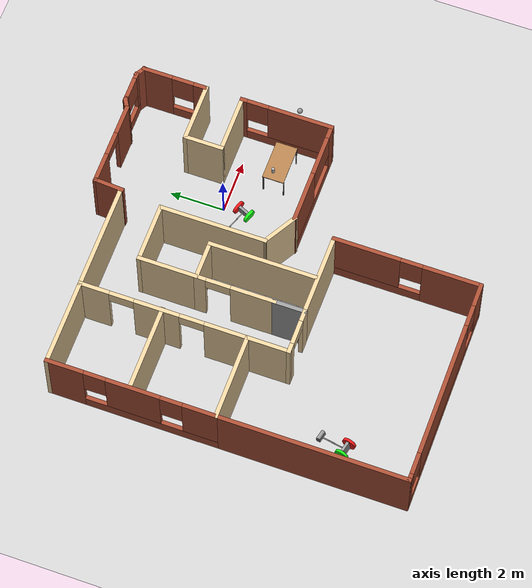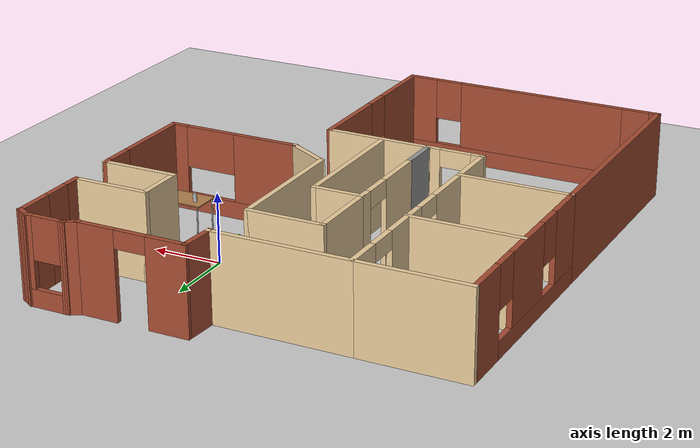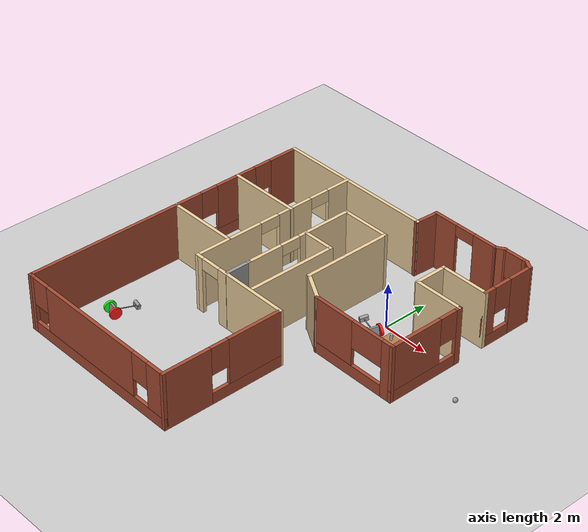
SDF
<sdf version="1.6">
 <world name="default">
  <plugin name="welcome_message" filename="libwelcome_message.so"/>
  <light name="sun" type="directional">
   <pose>0 0 10 0 -0 0</pose>
   <diffuse>0.8 0.8 0.8 1</diffuse>
   <specular>0.2 0.2 0.2 1</specular>
   <attenuation>
    <range>1000</range>
    <constant>0.9</constant>
    <linear>0.01</linear>
    <quadratic>0.001</quadratic>
   </attenuation>
   <direction>-0.5 0.1 -0.9</direction>
  </light>
  <model name="ground_plane">
   <static>1</static>
   <link name="link">
    <collision name="collision">
     <geometry><plane><normal>0 0 1</normal><size>100 100</size></plane></geometry>
     <surface><friction><ode><mu>100</mu><mu2>50</mu2></ode></friction></surface>
    </collision>
    <visual name="visual">
     <cast_shadows>0</cast_shadows>
     <geometry><plane><normal>0 0 1</normal><size>100 100</size></plane></geometry>
     <material>
      <script><uri>file://media/materials/scripts/gazebo.material</uri><name>Gazebo/Grey</name></script>
     </material>
    </visual>
   </link>
  </model>
  <gravity>0 0 -9.8</gravity>
  <magnetic_field>6e-06 2.3e-05 -4.2e-05</magnetic_field>
  <atmosphere type="adiabatic"/>
  <physics name="default_physics" default="0" type="ode">
   <max_step_size>0.001</max_step_size>
   <real_time_factor>1</real_time_factor>
   <real_time_update_rate>1000</real_time_update_rate>
  </physics>
  <scene><ambient>0.4 0.4 0.4 1</ambient><background>0.7 0.7 0.7 1</background><shadows>1</shadows></scene>
  <spherical_coordinates>
   <surface_model>EARTH_WGS84</surface_model>
   <latitude_deg>0</latitude_deg>
   <longitude_deg>0</longitude_deg>
   <elevation>0</elevation>
   <heading_deg>0</heading_deg>
  </spherical_coordinates>
  <model name="TwoWheelBalancer">
   <link name="link_0">
    <pose>0.012232 0 -0.27143 0 -0 0</pose>
    <inertial>
     <mass>1</mass>
     <inertia>
      <ixx>0.166667</ixx>
      <ixy>0</ixy>
      <ixz>0</ixz>
      <iyy>0.166667</iyy>
      <iyz>0</iyz>
      <izz>0.166667</izz>
     </inertia>
    </inertial>
    <visual name="visual">
     <geometry><box><size>0.4 0.4 0.1</size></box></geometry>
     <material>
      <lighting>1</lighting>
      <script><uri>file://media/materials/scripts/gazebo.material</uri><name>Gazebo/Grey</name></script>
      <shader type="pixel"><normal_map>__default__</normal_map></shader>
      <ambient>0.3 0.3 0.3 1</ambient>
      <diffuse>0.7 0.7 0.7 1</diffuse>
      <specular>0.01 0.01 0.01 1</specular>
      <emissive>0 0 0 1</emissive>
     </material>
    </visual>
    <collision name="collision">
     <geometry><box><size>0.4 0.4 0.1</size></box></geometry>
     <surface>
      <friction>
       <ode><mu>1</mu><mu2>1</mu2><fdir1>0 0 0</fdir1><slip1>0</slip1><slip2>0</slip2></ode>
       <torsional>
        <coefficient>1</coefficient>
        <patch_radius>0</patch_radius>
        <surface_radius>0</surface_radius>
        <use_patch_radius>1</use_patch_radius>
        <ode><slip>0</slip></ode>
       </torsional>
      </friction>
      <bounce><restitution_coefficient>0</restitution_coefficient><threshold>1e+06</threshold></bounce>
      <contact>
       <collide_without_contact>0</collide_without_contact>
       <collide_without_contact_bitmask>1</collide_without_contact_bitmask>
       <collide_bitmask>1</collide_bitmask>
       <ode>
        <soft_cfm>0</soft_cfm>
        <soft_erp>0.2</soft_erp>
        <kp>1e+13</kp>
        <kd>1</kd>
        <max_vel>0.01</max_vel>
        <min_depth>0</min_depth>
       </ode>
       <bullet>
        <split_impulse>1</split_impulse>
        <split_impulse_penetration_threshold>-0.01</split_impulse_penetration_threshold>
        <soft_cfm>0</soft_cfm>
        <soft_erp>0.2</soft_erp>
        <kp>1e+13</kp>
        <kd>1</kd>
       </bullet>
      </contact>
     </surface>
    </collision>
   </link>
   <link name="link_1">
    <pose>0.012232 0.250024 -0.27143 0 -0 0</pose>
    <inertial>
     <mass>1</mass>
     <inertia><ixx>0.145833</ixx><ixy>0</ixy><ixz>0</ixz><iyy>0.145833</iyy><iyz>0</iyz><izz>0.125</izz></inertia>
    </inertial>
    <visual name="visual">
     <pose>0 0 0 1.5707 -0 0</pose>
     <geometry><cylinder><radius>0.25</radius><length>0.1</length></cylinder></geometry>
     <material>
      <lighting>1</lighting>
      <script><uri>file://media/materials/scripts/gazebo.material</uri><name>Gazebo/Grey</name></script>
      <shader type="pixel"><normal_map>__default__</normal_map></shader>
      <ambient>0.1 1 0.1 1</ambient>
      <diffuse>0.1 1 0.1 1</diffuse>
      <specular>0.01 0.01 0.01 1</specular>
      <emissive>0 0 0 1</emissive>
     </material>
    </visual>
    <collision name="collision">
     <pose>0 0 0 1.5707 -0 0</pose>
     <geometry><cylinder><radius>0.25</radius><length>0.1</length></cylinder></geometry>
     <surface>
      <friction>
       <ode><mu>1</mu><mu2>1</mu2><fdir1>0 0 0</fdir1><slip1>0</slip1><slip2>0</slip2></ode>
       <torsional>
        <coefficient>1</coefficient>
        <patch_radius>0</patch_radius>
        <surface_radius>0</surface_radius>
        <use_patch_radius>1</use_patch_radius>
        <ode><slip>0</slip></ode>
       </torsional>
      </friction>
      <bounce><restitution_coefficient>0</restitution_coefficient><threshold>1e+06</threshold></bounce>
      <contact>
       <collide_without_contact>0</collide_without_contact>
       <collide_without_contact_bitmask>1</collide_without_contact_bitmask>
       <collide_bitmask>1</collide_bitmask>
       <ode>
        <soft_cfm>0</soft_cfm>
        <soft_erp>0.2</soft_erp>
        <kp>1e+13</kp>
        <kd>1</kd>
        <max_vel>0.01</max_vel>
        <min_depth>0</min_depth>
       </ode>
       <bullet>
        <split_impulse>1</split_impulse>
        <split_impulse_penetration_threshold>-0.01</split_impulse_penetration_threshold>
        <soft_cfm>0</soft_cfm>
        <soft_erp>0.2</soft_erp>
        <kp>1e+13</kp>
        <kd>1</kd>
       </bullet>
      </contact>
     </surface>
    </collision>
   </link>
   <link name="link_1_clone">
    <pose>0.012232 -0.250024 -0.27143 0 -0 0</pose>
    <inertial>
     <mass>1</mass>
     <inertia><ixx>0.145833</ixx><ixy>0</ixy><ixz>0</ixz><iyy>0.145833</iyy><iyz>0</iyz><izz>0.125</izz></inertia>
    </inertial>
    <visual name="visual">
     <pose>0 0 0 1.5707 -0 0</pose>
     <geometry><cylinder><radius>0.25</radius><length>0.1</length></cylinder></geometry>
     <material>
      <lighting>1</lighting>
      <script><uri>file://media/materials/scripts/gazebo.material</uri><name>Gazebo/Grey</name></script>
      <shader type="pixel"><normal_map>__default__</normal_map></shader>
      <ambient>1 0.1 0.1 1</ambient>
      <diffuse>1 0.1 0.1 1</diffuse>
      <specular>0.01 0.01 0.01 1</specular>
      <emissive>0 0 0 1</emissive>
     </material>
    </visual>
    <collision name="collision">
     <pose>0 0 0 1.5707 -0 0</pose>
     <geometry><cylinder><radius>0.25</radius><length>0.1</length></cylinder></geometry>
     <surface>
      <friction>
       <ode><mu>1</mu><mu2>1</mu2><fdir1>0 0 0</fdir1><slip1>0</slip1><slip2>0</slip2></ode>
       <torsional>
        <coefficient>1</coefficient>
        <patch_radius>0</patch_radius>
        <surface_radius>0</surface_radius>
        <use_patch_radius>1</use_patch_radius>
        <ode><slip>0</slip></ode>
       </torsional>
      </friction>
      <bounce><restitution_coefficient>0</restitution_coefficient><threshold>1e+06</threshold></bounce>
      <contact>
       <collide_without_contact>0</collide_without_contact>
       <collide_without_contact_bitmask>1</collide_without_contact_bitmask>
       <collide_bitmask>1</collide_bitmask>
       <ode>
        <soft_cfm>0</soft_cfm>
        <soft_erp>0.2</soft_erp>
        <kp>1e+13</kp>
        <kd>1</kd>
        <max_vel>0.01</max_vel>
        <min_depth>0</min_depth>
       </ode>
       <bullet>
        <split_impulse>1</split_impulse>
        <split_impulse_penetration_threshold>-0.01</split_impulse_penetration_threshold>
        <soft_cfm>0</soft_cfm>
        <soft_erp>0.2</soft_erp>
        <kp>1e+13</kp>
        <kd>1</kd>
       </bullet>
      </contact>
     </surface>
    </collision>
   </link>
   <link name="link_2">
    <pose>0.012232 0 -0.27143 0 -0 0</pose>
    <inertial>
     <mass>1</mass>
     <inertia><ixx>0.145833</ixx><ixy>0</ixy><ixz>0</ixz><iyy>0.145833</iyy><iyz>0</iyz><izz>0.125</izz></inertia>
    </inertial>
    <visual name="visual">
     <pose>0 0 0.5 0 -0 0</pose>
     <geometry><cylinder><radius>0.02</radius><length>1</length></cylinder></geometry>
     <material>
      <lighting>1</lighting>
      <script><uri>file://media/materials/scripts/gazebo.material</uri><name>Gazebo/Grey</name></script>
      <shader type="pixel"><normal_map>__default__</normal_map></shader>
      <ambient>0.3 0.3 0.3 1</ambient>
      <diffuse>0.7 0.7 0.7 1</diffuse>
      <specular>0.01 0.01 0.01 1</specular>
      <emissive>0 0 0 1</emissive>
     </material>
    </visual>
    <collision name="collision">
     <pose>0 0 0.5 0 -0 0</pose>
     <geometry><cylinder><radius>0.02</radius><length>1</length></cylinder></geometry>
     <surface>
      <friction>
       <ode><mu>1</mu><mu2>1</mu2><fdir1>0 0 0</fdir1><slip1>0</slip1><slip2>0</slip2></ode>
       <torsional>
        <coefficient>1</coefficient>
        <patch_radius>0</patch_radius>
        <surface_radius>0</surface_radius>
        <use_patch_radius>1</use_patch_radius>
        <ode><slip>0</slip></ode>
       </torsional>
      </friction>
      <bounce><restitution_coefficient>0</restitution_coefficient><threshold>1e+06</threshold></bounce>
      <contact>
       <collide_without_contact>0</collide_without_contact>
       <collide_without_contact_bitmask>1</collide_without_contact_bitmask>
       <collide_bitmask>1</collide_bitmask>
       <ode>
        <soft_cfm>0</soft_cfm>
        <soft_erp>0.2</soft_erp>
        <kp>1e+13</kp>
        <kd>1</kd>
        <max_vel>0.01</max_vel>
        <min_depth>0</min_depth>
       </ode>
       <bullet>
        <split_impulse>1</split_impulse>
        <split_impulse_penetration_threshold>-0.01</split_impulse_penetration_threshold>
        <soft_cfm>0</soft_cfm>
        <soft_erp>0.2</soft_erp>
        <kp>1e+13</kp>
        <kd>1</kd>
       </bullet>
      </contact>
     </surface>
    </collision>
   </link>
   <link name="link_3">
    <pose>0.012232 0 0.728572 0 -0 0</pose>
    <inertial>
     <mass>1</mass>
     <inertia>
      <ixx>0.166667</ixx>
      <ixy>0</ixy>
      <ixz>0</ixz>
      <iyy>0.166667</iyy>
      <iyz>0</iyz>
      <izz>0.166667</izz>
     </inertia>
    </inertial>
    <visual name="visual">
     <geometry><box><size>0.15 0.35 0.15</size></box></geometry>
     <material>
      <lighting>1</lighting>
      <script><uri>file://media/materials/scripts/gazebo.material</uri><name>Gazebo/Grey</name></script>
      <shader type="pixel"><normal_map>__default__</normal_map></shader>
      <ambient>0.3 0.3 0.3 1</ambient>
      <diffuse>0.7 0.7 0.7 1</diffuse>
      <specular>0.01 0.01 0.01 1</specular>
      <emissive>0 0 0 1</emissive>
     </material>
    </visual>
    <collision name="collision">
     <geometry><box><size>0.15 0.35 0.15</size></box></geometry>
     <surface>
      <friction>
       <ode><mu>1</mu><mu2>1</mu2><fdir1>0 0 0</fdir1><slip1>0</slip1><slip2>0</slip2></ode>
       <torsional>
        <coefficient>1</coefficient>
        <patch_radius>0</patch_radius>
        <surface_radius>0</surface_radius>
        <use_patch_radius>1</use_patch_radius>
        <ode><slip>0</slip></ode>
       </torsional>
      </friction>
      <bounce><restitution_coefficient>0</restitution_coefficient><threshold>1e+06</threshold></bounce>
      <contact>
       <collide_without_contact>0</collide_without_contact>
       <collide_without_contact_bitmask>1</collide_without_contact_bitmask>
       <collide_bitmask>1</collide_bitmask>
       <ode>
        <soft_cfm>0</soft_cfm>
        <soft_erp>0.2</soft_erp>
        <kp>1e+13</kp>
        <kd>1</kd>
        <max_vel>0.01</max_vel>
        <min_depth>0</min_depth>
       </ode>
       <bullet>
        <split_impulse>1</split_impulse>
        <split_impulse_penetration_threshold>-0.01</split_impulse_penetration_threshold>
        <soft_cfm>0</soft_cfm>
        <soft_erp>0.2</soft_erp>
        <kp>1e+13</kp>
        <kd>1</kd>
       </bullet>
      </contact>
     </surface>
    </collision>
   </link>
   <link name="link_5">
    <pose>0.092232 -0.12 0.728571 0 -0 0</pose>
    <inertial>
     <mass>1</mass>
     <inertia><ixx>0.145833</ixx><ixy>0</ixy><ixz>0</ixz><iyy>0.145833</iyy><iyz>0</iyz><izz>0.125</izz></inertia>
    </inertial>
    <visual name="visual">
     <pose>0 0 0 0 1.5707 0</pose>
     <geometry><cylinder><radius>0.025</radius><length>0.02</length></cylinder></geometry>
     <material>
      <lighting>1</lighting>
      <script><uri>file://media/materials/scripts/gazebo.material</uri><name>Gazebo/Grey</name></script>
      <shader type="pixel"><normal_map>__default__</normal_map></shader>
      <ambient>0 0 0 1</ambient>
      <diffuse>0 0 0 1</diffuse>
      <specular>0.01 0.01 0.01 1</specular>
      <emissive>0 0 0 1</emissive>
     </material>
    </visual>
    <collision name="collision">
     <geometry><cylinder><radius>0.025</radius><length>0.02</length></cylinder></geometry>
     <surface>
      <friction>
       <ode><mu>1</mu><mu2>1</mu2><fdir1>0 0 0</fdir1><slip1>0</slip1><slip2>0</slip2></ode>
       <torsional>
        <coefficient>1</coefficient>
        <patch_radius>0</patch_radius>
        <surface_radius>0</surface_radius>
        <use_patch_radius>1</use_patch_radius>
        <ode><slip>0</slip></ode>
       </torsional>
      </friction>
      <bounce><restitution_coefficient>0</restitution_coefficient><threshold>1e+06</threshold></bounce>
      <contact>
       <collide_without_contact>0</collide_without_contact>
       <collide_without_contact_bitmask>1</collide_without_contact_bitmask>
       <collide_bitmask>1</collide_bitmask>
       <ode>
        <soft_cfm>0</soft_cfm>
        <soft_erp>0.2</soft_erp>
        <kp>1e+13</kp>
        <kd>1</kd>
        <max_vel>0.01</max_vel>
        <min_depth>0</min_depth>
       </ode>
       <bullet>
        <split_impulse>1</split_impulse>
        <split_impulse_penetration_threshold>-0.01</split_impulse_penetration_threshold>
        <soft_cfm>0</soft_cfm>
        <soft_erp>0.2</soft_erp>
        <kp>1e+13</kp>
        <kd>1</kd>
       </bullet>
      </contact>
     </surface>
    </collision>
   </link>
   <link name="link_5_clone">
    <pose>0.092232 0.12 0.728571 0 -0 0</pose>
    <inertial>
     <mass>1</mass>
     <inertia><ixx>0.145833</ixx><ixy>0</ixy><ixz>0</ixz><iyy>0.145833</iyy><iyz>0</iyz><izz>0.125</izz></inertia>
    </inertial>
    <visual name="visual">
     <pose>0 0 0 0 1.5707 0</pose>
     <geometry><cylinder><radius>0.025</radius><length>0.02</length></cylinder></geometry>
     <material>
      <lighting>1</lighting>
      <script><uri>file://media/materials/scripts/gazebo.material</uri><name>Gazebo/Grey</name></script>
      <shader type="pixel"><normal_map>__default__</normal_map></shader>
      <ambient>0 0 0 1</ambient>
      <diffuse>0 0 0 1</diffuse>
      <specular>0.01 0.01 0.01 1</specular>
      <emissive>0 0 0 1</emissive>
     </material>
    </visual>
    <collision name="collision">
     <geometry><cylinder><radius>0.025</radius><length>0.02</length></cylinder></geometry>
     <surface>
      <friction>
       <ode><mu>1</mu><mu2>1</mu2><fdir1>0 0 0</fdir1><slip1>0</slip1><slip2>0</slip2></ode>
       <torsional>
        <coefficient>1</coefficient>
        <patch_radius>0</patch_radius>
        <surface_radius>0</surface_radius>
        <use_patch_radius>1</use_patch_radius>
        <ode><slip>0</slip></ode>
       </torsional>
      </friction>
      <bounce><restitution_coefficient>0</restitution_coefficient><threshold>1e+06</threshold></bounce>
      <contact>
       <collide_without_contact>0</collide_without_contact>
       <collide_without_contact_bitmask>1</collide_without_contact_bitmask>
       <collide_bitmask>1</collide_bitmask>
       <ode>
        <soft_cfm>0</soft_cfm>
        <soft_erp>0.2</soft_erp>
        <kp>1e+13</kp>
        <kd>1</kd>
        <max_vel>0.01</max_vel>
        <min_depth>0</min_depth>
       </ode>
       <bullet>
        <split_impulse>1</split_impulse>
        <split_impulse_penetration_threshold>-0.01</split_impulse_penetration_threshold>
        <soft_cfm>0</soft_cfm>
        <soft_erp>0.2</soft_erp>
        <kp>1e+13</kp>
        <kd>1</kd>
       </bullet>
      </contact>
     </surface>
    </collision>
   </link>
   <link name="link_6">
    <pose>-0.062768 -0 0.728572 1.57079 -0 0</pose>
    <inertial>
     <mass>1</mass>
     <inertia><ixx>0.145833</ixx><ixy>0</ixy><ixz>0</ixz><iyy>0.145833</iyy><iyz>0</iyz><izz>0.125</izz></inertia>
    </inertial>
    <visual name="visual">
     <geometry><cylinder><radius>0.075</radius><length>0.35</length></cylinder></geometry>
     <material>
      <lighting>1</lighting>
      <script><uri>file://media/materials/scripts/gazebo.material</uri><name>Gazebo/Grey</name></script>
      <shader type="pixel"><normal_map>__default__</normal_map></shader>
      <ambient>0.3 0.3 0.3 1</ambient>
      <diffuse>0.7 0.7 0.7 1</diffuse>
      <specular>0.01 0.01 0.01 1</specular>
      <emissive>0 0 0 1</emissive>
     </material>
    </visual>
    <collision name="collision">
     <geometry><cylinder><radius>0.075</radius><length>0.35</length></cylinder></geometry>
     <surface>
      <friction>
       <ode><mu>1</mu><mu2>1</mu2><fdir1>0 0 0</fdir1><slip1>0</slip1><slip2>0</slip2></ode>
       <torsional>
        <coefficient>1</coefficient>
        <patch_radius>0</patch_radius>
        <surface_radius>0</surface_radius>
        <use_patch_radius>1</use_patch_radius>
        <ode><slip>0</slip></ode>
       </torsional>
      </friction>
      <bounce><restitution_coefficient>0</restitution_coefficient><threshold>1e+06</threshold></bounce>
      <contact>
       <collide_without_contact>0</collide_without_contact>
       <collide_without_contact_bitmask>1</collide_without_contact_bitmask>
       <collide_bitmask>1</collide_bitmask>
       <ode>
        <soft_cfm>0</soft_cfm>
        <soft_erp>0.2</soft_erp>
        <kp>1e+13</kp>
        <kd>1</kd>
        <max_vel>0.01</max_vel>
        <min_depth>0</min_depth>
       </ode>
       <bullet>
        <split_impulse>1</split_impulse>
        <split_impulse_penetration_threshold>-0.01</split_impulse_penetration_threshold>
        <soft_cfm>0</soft_cfm>
        <soft_erp>0.2</soft_erp>
        <kp>1e+13</kp>
        <kd>1</kd>
       </bullet>
      </contact>
     </surface>
    </collision>
   </link>
   <joint name="link_0_JOINT_0" type="revolute">
    <parent>link_0</parent>
    <child>link_1</child>
    <axis>
     <xyz>0 0 1</xyz>
     <use_parent_model_frame>0</use_parent_model_frame>
     <limit>
      <lower>-1.79769e+308</lower>
      <upper>1.79769e+308</upper>
      <effort>-1</effort>
      <velocity>-1</velocity>
     </limit>
     <dynamics>
      <spring_reference>0</spring_reference>
      <spring_stiffness>0</spring_stiffness>
      <damping>0</damping>
      <friction>0</friction>
     </dynamics>
    </axis>
    <physics>
     <ode><limit><cfm>0</cfm><erp>0.2</erp></limit><suspension><cfm>0</cfm><erp>0.2</erp></suspension></ode>
    </physics>
   </joint>
   <joint name="link_0_JOINT_1" type="revolute">
    <parent>link_0</parent>
    <child>link_1_clone</child>
    <axis>
     <xyz>0 0 1</xyz>
     <use_parent_model_frame>0</use_parent_model_frame>
     <limit>
      <lower>-1.79769e+308</lower>
      <upper>1.79769e+308</upper>
      <effort>-1</effort>
      <velocity>-1</velocity>
     </limit>
     <dynamics>
      <spring_reference>0</spring_reference>
      <spring_stiffness>0</spring_stiffness>
      <damping>0</damping>
      <friction>0</friction>
     </dynamics>
    </axis>
    <physics>
     <ode><limit><cfm>0</cfm><erp>0.2</erp></limit><suspension><cfm>0</cfm><erp>0.2</erp></suspension></ode>
    </physics>
   </joint>
   <joint name="link_0_JOINT_2" type="fixed">
    <parent>link_0</parent>
    <child>link_2</child>
    <physics>
     <ode><limit><cfm>0</cfm><erp>0.2</erp></limit><suspension><cfm>0</cfm><erp>0.2</erp></suspension></ode>
    </physics>
   </joint>
   <joint name="link_2_JOINT_3" type="revolute">
    <parent>link_2</parent>
    <child>link_3</child>
    <axis>
     <xyz>1 0 0</xyz>
     <use_parent_model_frame>0</use_parent_model_frame>
     <limit>
      <lower>-1.79769e+308</lower>
      <upper>1.79769e+308</upper>
      <effort>-1</effort>
      <velocity>-1</velocity>
     </limit>
     <dynamics>
      <spring_reference>0</spring_reference>
      <spring_stiffness>0</spring_stiffness>
      <damping>0</damping>
      <friction>0</friction>
     </dynamics>
    </axis>
    <physics>
     <ode><limit><cfm>0</cfm><erp>0.2</erp></limit><suspension><cfm>0</cfm><erp>0.2</erp></suspension></ode>
    </physics>
   </joint>
   <joint name="link_3_JOINT_4" type="fixed">
    <parent>link_3</parent>
    <child>link_5</child>
    <physics>
     <ode><limit><cfm>0</cfm><erp>0.2</erp></limit><suspension><cfm>0</cfm><erp>0.2</erp></suspension></ode>
    </physics>
   </joint>
   <joint name="link_3_JOINT_5" type="fixed">
    <parent>link_3</parent>
    <child>link_5_clone</child>
    <physics>
     <ode><limit><cfm>0</cfm><erp>0.2</erp></limit><suspension><cfm>0</cfm><erp>0.2</erp></suspension></ode>
    </physics>
   </joint>
   <joint name="link_3_JOINT_6" type="fixed">
    <parent>link_3</parent>
    <child>link_6</child>
    <physics>
     <ode><limit><cfm>0</cfm><erp>0.2</erp></limit><suspension><cfm>0</cfm><erp>0.2</erp></suspension></ode>
    </physics>
   </joint>
   <static>0</static>
   <pose>-0.171429 -0.636532 0.205917 -2.39009 1.41798 0.377986</pose>
  </model>
  <model name="TwoWheelBalancer_0">
   <link name="link_0">
    <pose>0.012232 0 -0.27143 0 -0 0</pose>
    <inertial>
     <mass>1</mass>
     <inertia>
      <ixx>0.166667</ixx>
      <ixy>0</ixy>
      <ixz>0</ixz>
      <iyy>0.166667</iyy>
      <iyz>0</iyz>
      <izz>0.166667</izz>
     </inertia>
    </inertial>
    <visual name="visual">
     <geometry><box><size>0.4 0.4 0.1</size></box></geometry>
     <material>
      <lighting>1</lighting>
      <script><uri>file://media/materials/scripts/gazebo.material</uri><name>Gazebo/Grey</name></script>
      <shader type="pixel"><normal_map>__default__</normal_map></shader>
      <ambient>0.3 0.3 0.3 1</ambient>
      <diffuse>0.7 0.7 0.7 1</diffuse>
      <specular>0.01 0.01 0.01 1</specular>
      <emissive>0 0 0 1</emissive>
     </material>
    </visual>
    <collision name="collision">
     <geometry><box><size>0.4 0.4 0.1</size></box></geometry>
     <surface>
      <friction>
       <ode><mu>1</mu><mu2>1</mu2><fdir1>0 0 0</fdir1><slip1>0</slip1><slip2>0</slip2></ode>
       <torsional>
        <coefficient>1</coefficient>
        <patch_radius>0</patch_radius>
        <surface_radius>0</surface_radius>
        <use_patch_radius>1</use_patch_radius>
        <ode><slip>0</slip></ode>
       </torsional>
      </friction>
      <bounce><restitution_coefficient>0</restitution_coefficient><threshold>1e+06</threshold></bounce>
      <contact>
       <collide_without_contact>0</collide_without_contact>
       <collide_without_contact_bitmask>1</collide_without_contact_bitmask>
       <collide_bitmask>1</collide_bitmask>
       <ode>
        <soft_cfm>0</soft_cfm>
        <soft_erp>0.2</soft_erp>
        <kp>1e+13</kp>
        <kd>1</kd>
        <max_vel>0.01</max_vel>
        <min_depth>0</min_depth>
       </ode>
       <bullet>
        <split_impulse>1</split_impulse>
        <split_impulse_penetration_threshold>-0.01</split_impulse_penetration_threshold>
        <soft_cfm>0</soft_cfm>
        <soft_erp>0.2</soft_erp>
        <kp>1e+13</kp>
        <kd>1</kd>
       </bullet>
      </contact>
     </surface>
    </collision>
   </link>
   <link name="link_1">
    <pose>0.012232 0.250024 -0.27143 0 -0 0</pose>
    <inertial>
     <mass>1</mass>
     <inertia><ixx>0.145833</ixx><ixy>0</ixy><ixz>0</ixz><iyy>0.145833</iyy><iyz>0</iyz><izz>0.125</izz></inertia>
    </inertial>
    <visual name="visual">
     <pose>0 0 0 1.5707 -0 0</pose>
     <geometry><cylinder><radius>0.25</radius><length>0.1</length></cylinder></geometry>
     <material>
      <lighting>1</lighting>
      <script><uri>file://media/materials/scripts/gazebo.material</uri><name>Gazebo/Grey</name></script>
      <shader type="pixel"><normal_map>__default__</normal_map></shader>
      <ambient>0.1 1 0.1 1</ambient>
      <diffuse>0.1 1 0.1 1</diffuse>
      <specular>0.01 0.01 0.01 1</specular>
      <emissive>0 0 0 1</emissive>
     </material>
    </visual>
    <collision name="collision">
     <pose>0 0 0 1.5707 -0 0</pose>
     <geometry><cylinder><radius>0.25</radius><length>0.1</length></cylinder></geometry>
     <surface>
      <friction>
       <ode><mu>1</mu><mu2>1</mu2><fdir1>0 0 0</fdir1><slip1>0</slip1><slip2>0</slip2></ode>
       <torsional>
        <coefficient>1</coefficient>
        <patch_radius>0</patch_radius>
        <surface_radius>0</surface_radius>
        <use_patch_radius>1</use_patch_radius>
        <ode><slip>0</slip></ode>
       </torsional>
      </friction>
      <bounce><restitution_coefficient>0</restitution_coefficient><threshold>1e+06</threshold></bounce>
      <contact>
       <collide_without_contact>0</collide_without_contact>
       <collide_without_contact_bitmask>1</collide_without_contact_bitmask>
       <collide_bitmask>1</collide_bitmask>
       <ode>
        <soft_cfm>0</soft_cfm>
        <soft_erp>0.2</soft_erp>
        <kp>1e+13</kp>
        <kd>1</kd>
        <max_vel>0.01</max_vel>
        <min_depth>0</min_depth>
       </ode>
       <bullet>
        <split_impulse>1</split_impulse>
        <split_impulse_penetration_threshold>-0.01</split_impulse_penetration_threshold>
        <soft_cfm>0</soft_cfm>
        <soft_erp>0.2</soft_erp>
        <kp>1e+13</kp>
        <kd>1</kd>
       </bullet>
      </contact>
     </surface>
    </collision>
   </link>
   <link name="link_1_clone">
    <pose>0.012232 -0.250024 -0.27143 0 -0 0</pose>
    <inertial>
     <mass>1</mass>
     <inertia><ixx>0.145833</ixx><ixy>0</ixy><ixz>0</ixz><iyy>0.145833</iyy><iyz>0</iyz><izz>0.125</izz></inertia>
    </inertial>
    <visual name="visual">
     <pose>0 0 0 1.5707 -0 0</pose>
     <geometry><cylinder><radius>0.25</radius><length>0.1</length></cylinder></geometry>
     <material>
      <lighting>1</lighting>
      <script><uri>file://media/materials/scripts/gazebo.material</uri><name>Gazebo/Grey</name></script>
      <shader type="pixel"><normal_map>__default__</normal_map></shader>
      <ambient>1 0.1 0.1 1</ambient>
      <diffuse>1 0.1 0.1 1</diffuse>
      <specular>0.01 0.01 0.01 1</specular>
      <emissive>0 0 0 1</emissive>
     </material>
    </visual>
    <collision name="collision">
     <pose>0 0 0 1.5707 -0 0</pose>
     <geometry><cylinder><radius>0.25</radius><length>0.1</length></cylinder></geometry>
     <surface>
      <friction>
       <ode><mu>1</mu><mu2>1</mu2><fdir1>0 0 0</fdir1><slip1>0</slip1><slip2>0</slip2></ode>
       <torsional>
        <coefficient>1</coefficient>
        <patch_radius>0</patch_radius>
        <surface_radius>0</surface_radius>
        <use_patch_radius>1</use_patch_radius>
        <ode><slip>0</slip></ode>
       </torsional>
      </friction>
      <bounce><restitution_coefficient>0</restitution_coefficient><threshold>1e+06</threshold></bounce>
      <contact>
       <collide_without_contact>0</collide_without_contact>
       <collide_without_contact_bitmask>1</collide_without_contact_bitmask>
       <collide_bitmask>1</collide_bitmask>
       <ode>
        <soft_cfm>0</soft_cfm>
        <soft_erp>0.2</soft_erp>
        <kp>1e+13</kp>
        <kd>1</kd>
        <max_vel>0.01</max_vel>
        <min_depth>0</min_depth>
       </ode>
       <bullet>
        <split_impulse>1</split_impulse>
        <split_impulse_penetration_threshold>-0.01</split_impulse_penetration_threshold>
        <soft_cfm>0</soft_cfm>
        <soft_erp>0.2</soft_erp>
        <kp>1e+13</kp>
        <kd>1</kd>
       </bullet>
      </contact>
     </surface>
    </collision>
   </link>
   <link name="link_2">
    <pose>0.012232 0 -0.27143 0 -0 0</pose>
    <inertial>
     <mass>1</mass>
     <inertia><ixx>0.145833</ixx><ixy>0</ixy><ixz>0</ixz><iyy>0.145833</iyy><iyz>0</iyz><izz>0.125</izz></inertia>
    </inertial>
    <visual name="visual">
     <pose>0 0 0.5 0 -0 0</pose>
     <geometry><cylinder><radius>0.02</radius><length>1</length></cylinder></geometry>
     <material>
      <lighting>1</lighting>
      <script><uri>file://media/materials/scripts/gazebo.material</uri><name>Gazebo/Grey</name></script>
      <shader type="pixel"><normal_map>__default__</normal_map></shader>
      <ambient>0.3 0.3 0.3 1</ambient>
      <diffuse>0.7 0.7 0.7 1</diffuse>
      <specular>0.01 0.01 0.01 1</specular>
      <emissive>0 0 0 1</emissive>
     </material>
    </visual>
    <collision name="collision">
     <pose>0 0 0.5 0 -0 0</pose>
     <geometry><cylinder><radius>0.02</radius><length>1</length></cylinder></geometry>
     <surface>
      <friction>
       <ode><mu>1</mu><mu2>1</mu2><fdir1>0 0 0</fdir1><slip1>0</slip1><slip2>0</slip2></ode>
       <torsional>
        <coefficient>1</coefficient>
        <patch_radius>0</patch_radius>
        <surface_radius>0</surface_radius>
        <use_patch_radius>1</use_patch_radius>
        <ode><slip>0</slip></ode>
       </torsional>
      </friction>
      <bounce><restitution_coefficient>0</restitution_coefficient><threshold>1e+06</threshold></bounce>
      <contact>
       <collide_without_contact>0</collide_without_contact>
       <collide_without_contact_bitmask>1</collide_without_contact_bitmask>
       <collide_bitmask>1</collide_bitmask>
       <ode>
        <soft_cfm>0</soft_cfm>
        <soft_erp>0.2</soft_erp>
        <kp>1e+13</kp>
        <kd>1</kd>
        <max_vel>0.01</max_vel>
        <min_depth>0</min_depth>
       </ode>
       <bullet>
        <split_impulse>1</split_impulse>
        <split_impulse_penetration_threshold>-0.01</split_impulse_penetration_threshold>
        <soft_cfm>0</soft_cfm>
        <soft_erp>0.2</soft_erp>
        <kp>1e+13</kp>
        <kd>1</kd>
       </bullet>
      </contact>
     </surface>
    </collision>
   </link>
   <link name="link_3">
    <pose>0.012232 0 0.728572 0 -0 0</pose>
    <inertial>
     <mass>1</mass>
     <inertia>
      <ixx>0.166667</ixx>
      <ixy>0</ixy>
      <ixz>0</ixz>
      <iyy>0.166667</iyy>
      <iyz>0</iyz>
      <izz>0.166667</izz>
     </inertia>
    </inertial>
    <visual name="visual">
     <geometry><box><size>0.15 0.35 0.15</size></box></geometry>
     <material>
      <lighting>1</lighting>
      <script><uri>file://media/materials/scripts/gazebo.material</uri><name>Gazebo/Grey</name></script>
      <shader type="pixel"><normal_map>__default__</normal_map></shader>
      <ambient>0.3 0.3 0.3 1</ambient>
      <diffuse>0.7 0.7 0.7 1</diffuse>
      <specular>0.01 0.01 0.01 1</specular>
      <emissive>0 0 0 1</emissive>
     </material>
    </visual>
    <collision name="collision">
     <geometry><box><size>0.15 0.35 0.15</size></box></geometry>
     <surface>
      <friction>
       <ode><mu>1</mu><mu2>1</mu2><fdir1>0 0 0</fdir1><slip1>0</slip1><slip2>0</slip2></ode>
       <torsional>
        <coefficient>1</coefficient>
        <patch_radius>0</patch_radius>
        <surface_radius>0</surface_radius>
        <use_patch_radius>1</use_patch_radius>
        <ode><slip>0</slip></ode>
       </torsional>
      </friction>
      <bounce><restitution_coefficient>0</restitution_coefficient><threshold>1e+06</threshold></bounce>
      <contact>
       <collide_without_contact>0</collide_without_contact>
       <collide_without_contact_bitmask>1</collide_without_contact_bitmask>
       <collide_bitmask>1</collide_bitmask>
       <ode>
        <soft_cfm>0</soft_cfm>
        <soft_erp>0.2</soft_erp>
        <kp>1e+13</kp>
        <kd>1</kd>
        <max_vel>0.01</max_vel>
        <min_depth>0</min_depth>
       </ode>
       <bullet>
        <split_impulse>1</split_impulse>
        <split_impulse_penetration_threshold>-0.01</split_impulse_penetration_threshold>
        <soft_cfm>0</soft_cfm>
        <soft_erp>0.2</soft_erp>
        <kp>1e+13</kp>
        <kd>1</kd>
       </bullet>
      </contact>
     </surface>
    </collision>
   </link>
   <link name="link_5">
    <pose>0.092232 -0.12 0.728571 0 -0 0</pose>
    <inertial>
     <mass>1</mass>
     <inertia><ixx>0.145833</ixx><ixy>0</ixy><ixz>0</ixz><iyy>0.145833</iyy><iyz>0</iyz><izz>0.125</izz></inertia>
    </inertial>
    <visual name="visual">
     <pose>0 0 0 0 1.5707 0</pose>
     <geometry><cylinder><radius>0.025</radius><length>0.02</length></cylinder></geometry>
     <material>
      <lighting>1</lighting>
      <script><uri>file://media/materials/scripts/gazebo.material</uri><name>Gazebo/Grey</name></script>
      <shader type="pixel"><normal_map>__default__</normal_map></shader>
      <ambient>0 0 0 1</ambient>
      <diffuse>0 0 0 1</diffuse>
      <specular>0.01 0.01 0.01 1</specular>
      <emissive>0 0 0 1</emissive>
     </material>
    </visual>
    <collision name="collision">
     <geometry><cylinder><radius>0.025</radius><length>0.02</length></cylinder></geometry>
     <surface>
      <friction>
       <ode><mu>1</mu><mu2>1</mu2><fdir1>0 0 0</fdir1><slip1>0</slip1><slip2>0</slip2></ode>
       <torsional>
        <coefficient>1</coefficient>
        <patch_radius>0</patch_radius>
        <surface_radius>0</surface_radius>
        <use_patch_radius>1</use_patch_radius>
        <ode><slip>0</slip></ode>
       </torsional>
      </friction>
      <bounce><restitution_coefficient>0</restitution_coefficient><threshold>1e+06</threshold></bounce>
      <contact>
       <collide_without_contact>0</collide_without_contact>
       <collide_without_contact_bitmask>1</collide_without_contact_bitmask>
       <collide_bitmask>1</collide_bitmask>
       <ode>
        <soft_cfm>0</soft_cfm>
        <soft_erp>0.2</soft_erp>
        <kp>1e+13</kp>
        <kd>1</kd>
        <max_vel>0.01</max_vel>
        <min_depth>0</min_depth>
       </ode>
       <bullet>
        <split_impulse>1</split_impulse>
        <split_impulse_penetration_threshold>-0.01</split_impulse_penetration_threshold>
        <soft_cfm>0</soft_cfm>
        <soft_erp>0.2</soft_erp>
        <kp>1e+13</kp>
        <kd>1</kd>
       </bullet>
      </contact>
     </surface>
    </collision>
   </link>
   <link name="link_5_clone">
    <pose>0.092232 0.12 0.728571 0 -0 0</pose>
    <inertial>
     <mass>1</mass>
     <inertia><ixx>0.145833</ixx><ixy>0</ixy><ixz>0</ixz><iyy>0.145833</iyy><iyz>0</iyz><izz>0.125</izz></inertia>
    </inertial>
    <visual name="visual">
     <pose>0 0 0 0 1.5707 0</pose>
     <geometry><cylinder><radius>0.025</radius><length>0.02</length></cylinder></geometry>
     <material>
      <lighting>1</lighting>
      <script><uri>file://media/materials/scripts/gazebo.material</uri><name>Gazebo/Grey</name></script>
      <shader type="pixel"><normal_map>__default__</normal_map></shader>
      <ambient>0 0 0 1</ambient>
      <diffuse>0 0 0 1</diffuse>
      <specular>0.01 0.01 0.01 1</specular>
      <emissive>0 0 0 1</emissive>
     </material>
    </visual>
    <collision name="collision">
     <geometry><cylinder><radius>0.025</radius><length>0.02</length></cylinder></geometry>
     <surface>
      <friction>
       <ode><mu>1</mu><mu2>1</mu2><fdir1>0 0 0</fdir1><slip1>0</slip1><slip2>0</slip2></ode>
       <torsional>
        <coefficient>1</coefficient>
        <patch_radius>0</patch_radius>
        <surface_radius>0</surface_radius>
        <use_patch_radius>1</use_patch_radius>
        <ode><slip>0</slip></ode>
       </torsional>
      </friction>
      <bounce><restitution_coefficient>0</restitution_coefficient><threshold>1e+06</threshold></bounce>
      <contact>
       <collide_without_contact>0</collide_without_contact>
       <collide_without_contact_bitmask>1</collide_without_contact_bitmask>
       <collide_bitmask>1</collide_bitmask>
       <ode>
        <soft_cfm>0</soft_cfm>
        <soft_erp>0.2</soft_erp>
        <kp>1e+13</kp>
        <kd>1</kd>
        <max_vel>0.01</max_vel>
        <min_depth>0</min_depth>
       </ode>
       <bullet>
        <split_impulse>1</split_impulse>
        <split_impulse_penetration_threshold>-0.01</split_impulse_penetration_threshold>
        <soft_cfm>0</soft_cfm>
        <soft_erp>0.2</soft_erp>
        <kp>1e+13</kp>
        <kd>1</kd>
       </bullet>
      </contact>
     </surface>
    </collision>
   </link>
   <link name="link_6">
    <pose>-0.062768 -0 0.728572 1.57079 -0 0</pose>
    <inertial>
     <mass>1</mass>
     <inertia><ixx>0.145833</ixx><ixy>0</ixy><ixz>0</ixz><iyy>0.145833</iyy><iyz>0</iyz><izz>0.125</izz></inertia>
    </inertial>
    <visual name="visual">
     <geometry><cylinder><radius>0.075</radius><length>0.35</length></cylinder></geometry>
     <material>
      <lighting>1</lighting>
      <script><uri>file://media/materials/scripts/gazebo.material</uri><name>Gazebo/Grey</name></script>
      <shader type="pixel"><normal_map>__default__</normal_map></shader>
      <ambient>0.3 0.3 0.3 1</ambient>
      <diffuse>0.7 0.7 0.7 1</diffuse>
      <specular>0.01 0.01 0.01 1</specular>
      <emissive>0 0 0 1</emissive>
     </material>
    </visual>
    <collision name="collision">
     <geometry><cylinder><radius>0.075</radius><length>0.35</length></cylinder></geometry>
     <surface>
      <friction>
       <ode><mu>1</mu><mu2>1</mu2><fdir1>0 0 0</fdir1><slip1>0</slip1><slip2>0</slip2></ode>
       <torsional>
        <coefficient>1</coefficient>
        <patch_radius>0</patch_radius>
        <surface_radius>0</surface_radius>
        <use_patch_radius>1</use_patch_radius>
        <ode><slip>0</slip></ode>
       </torsional>
      </friction>
      <bounce><restitution_coefficient>0</restitution_coefficient><threshold>1e+06</threshold></bounce>
      <contact>
       <collide_without_contact>0</collide_without_contact>
       <collide_without_contact_bitmask>1</collide_without_contact_bitmask>
       <collide_bitmask>1</collide_bitmask>
       <ode>
        <soft_cfm>0</soft_cfm>
        <soft_erp>0.2</soft_erp>
        <kp>1e+13</kp>
        <kd>1</kd>
        <max_vel>0.01</max_vel>
        <min_depth>0</min_depth>
       </ode>
       <bullet>
        <split_impulse>1</split_impulse>
        <split_impulse_penetration_threshold>-0.01</split_impulse_penetration_threshold>
        <soft_cfm>0</soft_cfm>
        <soft_erp>0.2</soft_erp>
        <kp>1e+13</kp>
        <kd>1</kd>
       </bullet>
      </contact>
     </surface>
    </collision>
   </link>
   <joint name="link_0_JOINT_0" type="revolute">
    <parent>link_0</parent>
    <child>link_1</child>
    <axis>
     <xyz>0 0 1</xyz>
     <use_parent_model_frame>0</use_parent_model_frame>
     <limit>
      <lower>-1.79769e+308</lower>
      <upper>1.79769e+308</upper>
      <effort>-1</effort>
      <velocity>-1</velocity>
     </limit>
     <dynamics>
      <spring_reference>0</spring_reference>
      <spring_stiffness>0</spring_stiffness>
      <damping>0</damping>
      <friction>0</friction>
     </dynamics>
    </axis>
    <physics>
     <ode><limit><cfm>0</cfm><erp>0.2</erp></limit><suspension><cfm>0</cfm><erp>0.2</erp></suspension></ode>
    </physics>
   </joint>
   <joint name="link_0_JOINT_1" type="revolute">
    <parent>link_0</parent>
    <child>link_1_clone</child>
    <axis>
     <xyz>0 0 1</xyz>
     <use_parent_model_frame>0</use_parent_model_frame>
     <limit>
      <lower>-1.79769e+308</lower>
      <upper>1.79769e+308</upper>
      <effort>-1</effort>
      <velocity>-1</velocity>
     </limit>
     <dynamics>
      <spring_reference>0</spring_reference>
      <spring_stiffness>0</spring_stiffness>
      <damping>0</damping>
      <friction>0</friction>
     </dynamics>
    </axis>
    <physics>
     <ode><limit><cfm>0</cfm><erp>0.2</erp></limit><suspension><cfm>0</cfm><erp>0.2</erp></suspension></ode>
    </physics>
   </joint>
   <joint name="link_0_JOINT_2" type="fixed">
    <parent>link_0</parent>
    <child>link_2</child>
    <physics>
     <ode><limit><cfm>0</cfm><erp>0.2</erp></limit><suspension><cfm>0</cfm><erp>0.2</erp></suspension></ode>
    </physics>
   </joint>
   <joint name="link_2_JOINT_3" type="revolute">
    <parent>link_2</parent>
    <child>link_3</child>
    <axis>
     <xyz>1 0 0</xyz>
     <use_parent_model_frame>0</use_parent_model_frame>
     <limit>
      <lower>-1.79769e+308</lower>
      <upper>1.79769e+308</upper>
      <effort>-1</effort>
      <velocity>-1</velocity>
     </limit>
     <dynamics>
      <spring_reference>0</spring_reference>
      <spring_stiffness>0</spring_stiffness>
      <damping>0</damping>
      <friction>0</friction>
     </dynamics>
    </axis>
    <physics>
     <ode><limit><cfm>0</cfm><erp>0.2</erp></limit><suspension><cfm>0</cfm><erp>0.2</erp></suspension></ode>
    </physics>
   </joint>
   <joint name="link_3_JOINT_4" type="fixed">
    <parent>link_3</parent>
    <child>link_5</child>
    <physics>
     <ode><limit><cfm>0</cfm><erp>0.2</erp></limit><suspension><cfm>0</cfm><erp>0.2</erp></suspension></ode>
    </physics>
   </joint>
   <joint name="link_3_JOINT_5" type="fixed">
    <parent>link_3</parent>
    <child>link_5_clone</child>
    <physics>
     <ode><limit><cfm>0</cfm><erp>0.2</erp></limit><suspension><cfm>0</cfm><erp>0.2</erp></suspension></ode>
    </physics>
   </joint>
   <joint name="link_3_JOINT_6" type="fixed">
    <parent>link_3</parent>
    <child>link_6</child>
    <physics>
     <ode><limit><cfm>0</cfm><erp>0.2</erp></limit><suspension><cfm>0</cfm><erp>0.2</erp></suspension></ode>
    </physics>
   </joint>
   <static>0</static>
   <pose>-7.32432 -6.8861 0.223581 3.1135 1.42453 -1.82903</pose>
  </model>
  <model name="Silversprings">
   <pose>-2.73372 -2.72178 0 0 -0 0</pose>
   <link name="Wall_0">
    <pose>2.65627 6.86127 0 0 -0 0</pose>
    <visual name="Wall_0_Visual_0">
     <pose>-1.02638 0 1.25 0 -0 0</pose>
     <geometry><box><size>1.16439 0.15 2.5</size></box></geometry>
     <material>
      <script><uri>file://media/materials/scripts/gazebo.material</uri><name>Gazebo/Bricks</name></script>
      <ambient>1 1 1 1</ambient>
     </material>
     <meta><layer>0</layer></meta>
    </visual>
    <collision name="Wall_0_Collision_0">
     <geometry><box><size>1.16439 0.15 2.5</size></box></geometry>
     <pose>-1.02638 0 1.25 0 -0 0</pose>
    </collision>
    <visual name="Wall_0_Visual_1">
     <pose>1.0322 0 1.25 0 -0 0</pose>
     <geometry><box><size>1.15276 0.15 2.5</size></box></geometry>
     <material>
      <script><uri>file://media/materials/scripts/gazebo.material</uri><name>Gazebo/Bricks</name></script>
      <ambient>1 1 1 1</ambient>
     </material>
     <meta><layer>0</layer></meta>
    </visual>
    <collision name="Wall_0_Collision_1">
     <geometry><box><size>1.15276 0.15 2.5</size></box></geometry>
     <pose>1.0322 0 1.25 0 -0 0</pose>
    </collision>
    <visual name="Wall_0_Visual_2">
     <pose>0.005815 0 2.25 0 -0 0</pose>
     <geometry><box><size>0.9 0.15 0.5</size></box></geometry>
     <material>
      <script><uri>file://media/materials/scripts/gazebo.material</uri><name>Gazebo/Bricks</name></script>
      <ambient>1 1 1 1</ambient>
     </material>
     <meta><layer>0</layer></meta>
    </visual>
    <collision name="Wall_0_Collision_2">
     <geometry><box><size>0.9 0.15 0.5</size></box></geometry>
     <pose>0.005815 0 2.25 0 -0 0</pose>
    </collision>
   </link>
   <link name="Wall_1">
    <collision name="Wall_1_Collision">
     <geometry><box><size>0.5 0.15 2.5</size></box></geometry>
     <pose>0 0 1.25 0 -0 0</pose>
    </collision>
    <visual name="Wall_1_Visual">
     <pose>0 0 1.25 0 -0 0</pose>
     <geometry><box><size>0.5 0.15 2.5</size></box></geometry>
     <material>
      <script><uri>file://media/materials/scripts/gazebo.material</uri><name>Gazebo/Bricks</name></script>
      <ambient>1 1 1 1</ambient>
     </material>
     <meta><layer>0</layer></meta>
    </visual>
    <pose>4.34118 6.94877 0 0 -0 0.523599</pose>
   </link>
   <link name="Wall_10">
    <collision name="Wall_10_Collision">
     <geometry><box><size>2.25 0.15 2.5</size></box></geometry>
     <pose>0 0 1.25 0 -0 0</pose>
    </collision>
    <visual name="Wall_10_Visual">
     <pose>0 0 1.25 0 -0 0</pose>
     <geometry><box><size>2.25 0.15 2.5</size></box></geometry>
     <material>
      <script><uri>file://media/materials/scripts/gazebo.material</uri><name>Gazebo/Grey</name></script>
      <ambient>0.921569 0.807843 0.615686 1</ambient>
     </material>
     <meta><layer>0</layer></meta>
    </visual>
    <pose>4.84584 3.16127 0 0 -0 0</pose>
   </link>
   <link name="Wall_14">
    <pose>5.89584 1.48627 0 0 0 -1.5708</pose>
    <visual name="Wall_14_Visual_0">
     <pose>-1.61318 0 1.25 0 -0 0</pose>
     <geometry><box><size>0.273643 0.15 2.5</size></box></geometry>
     <material>
      <script><uri>file://media/materials/scripts/gazebo.material</uri><name>Gazebo/Bricks</name></script>
      <ambient>1 1 1 1</ambient>
     </material>
     <meta><layer>0</layer></meta>
    </visual>
    <collision name="Wall_14_Collision_0">
     <geometry><box><size>0.273643 0.15 2.5</size></box></geometry>
     <pose>-1.61318 0 1.25 0 -0 0</pose>
    </collision>
    <visual name="Wall_14_Visual_1">
     <pose>0.136822 0 0.25 0 -0 0</pose>
     <geometry><box><size>3.22636 0.15 0.5</size></box></geometry>
     <material>
      <script><uri>file://media/materials/scripts/gazebo.material</uri><name>Gazebo/Bricks</name></script>
      <ambient>1 1 1 1</ambient>
     </material>
     <meta><layer>0</layer></meta>
    </visual>
    <collision name="Wall_14_Collision_1">
     <geometry><box><size>3.22636 0.15 0.5</size></box></geometry>
     <pose>0.136822 0 0.25 0 -0 0</pose>
    </collision>
    <visual name="Wall_14_Visual_2">
     <pose>0.536822 0 1.5 0 -0 0</pose>
     <geometry><box><size>2.42636 0.15 2</size></box></geometry>
     <material>
      <script><uri>file://media/materials/scripts/gazebo.material</uri><name>Gazebo/Bricks</name></script>
      <ambient>1 1 1 1</ambient>
     </material>
     <meta><layer>0</layer></meta>
    </visual>
    <collision name="Wall_14_Collision_2">
     <geometry><box><size>2.42636 0.15 2</size></box></geometry>
     <pose>0.536822 0 1.5 0 -0 0</pose>
    </collision>
    <visual name="Wall_14_Visual_3">
     <pose>-1.07636 0 1.9 0 -0 0</pose>
     <geometry><box><size>0.8 0.15 1.2</size></box></geometry>
     <material>
      <script><uri>file://media/materials/scripts/gazebo.material</uri><name>Gazebo/Bricks</name></script>
      <ambient>1 1 1 1</ambient>
     </material>
     <meta><layer>0</layer></meta>
    </visual>
    <collision name="Wall_14_Collision_3">
     <geometry><box><size>0.8 0.15 1.2</size></box></geometry>
     <pose>-1.07636 0 1.9 0 -0 0</pose>
    </collision>
   </link>
   <link name="Wall_15">
    <pose>3.97084 -0.188725 0 0 -0 3.14159</pose>
    <visual name="Wall_15_Visual_0">
     <pose>-1.7298 0 1.25 0 -0 0</pose>
     <geometry><box><size>0.540398 0.15 2.5</size></box></geometry>
     <material>
      <script><uri>file://media/materials/scripts/gazebo.material</uri><name>Gazebo/Bricks</name></script>
      <ambient>1 1 1 1</ambient>
     </material>
     <meta><layer>0</layer></meta>
    </visual>
    <collision name="Wall_15_Collision_0">
     <geometry><box><size>0.540398 0.15 2.5</size></box></geometry>
     <pose>-1.7298 0 1.25 0 -0 0</pose>
    </collision>
    <visual name="Wall_15_Visual_1">
     <pose>0.270199 0 0.25 0 -0 0</pose>
     <geometry><box><size>3.4596 0.15 0.5</size></box></geometry>
     <material>
      <script><uri>file://media/materials/scripts/gazebo.material</uri><name>Gazebo/Bricks</name></script>
      <ambient>1 1 1 1</ambient>
     </material>
     <meta><layer>0</layer></meta>
    </visual>
    <collision name="Wall_15_Collision_1">
     <geometry><box><size>3.4596 0.15 0.5</size></box></geometry>
     <pose>0.270199 0 0.25 0 -0 0</pose>
    </collision>
    <visual name="Wall_15_Visual_2">
     <pose>1.0202 0 1.5 0 -0 0</pose>
     <geometry><box><size>1.9596 0.15 2</size></box></geometry>
     <material>
      <script><uri>file://media/materials/scripts/gazebo.material</uri><name>Gazebo/Bricks</name></script>
      <ambient>1 1 1 1</ambient>
     </material>
     <meta><layer>0</layer></meta>
    </visual>
    <collision name="Wall_15_Collision_2">
     <geometry><box><size>1.9596 0.15 2</size></box></geometry>
     <pose>1.0202 0 1.5 0 -0 0</pose>
    </collision>
    <visual name="Wall_15_Visual_3">
     <pose>-0.709602 0 1.9 0 -0 0</pose>
     <geometry><box><size>1.5 0.15 1.2</size></box></geometry>
     <material>
      <script><uri>file://media/materials/scripts/gazebo.material</uri><name>Gazebo/Bricks</name></script>
      <ambient>1 1 1 1</ambient>
     </material>
     <meta><layer>0</layer></meta>
    </visual>
    <collision name="Wall_15_Collision_3">
     <geometry><box><size>1.5 0.15 1.2</size></box></geometry>
     <pose>-0.709602 0 1.9 0 -0 0</pose>
    </collision>
   </link>
   <link name="Wall_16">
    <collision name="Wall_16_Collision">
     <geometry><box><size>1.5 0.15 2.5</size></box></geometry>
     <pose>0 0 1.25 0 -0 0</pose>
    </collision>
    <visual name="Wall_16_Visual">
     <pose>0 0 1.25 0 -0 0</pose>
     <geometry><box><size>1.5 0.15 2.5</size></box></geometry>
     <material>
      <script><uri>file://media/materials/scripts/gazebo.material</uri><name>Gazebo/Grey</name></script>
      <ambient>0.921569 0.807843 0.615686 1</ambient>
     </material>
     <meta><layer>0</layer></meta>
    </visual>
    <pose>1.46128 0.148774 0 0 -0 2.61799</pose>
   </link>
   <link name="Wall_17">
    <collision name="Wall_17_Collision">
     <geometry><box><size>4 0.15 2.5</size></box></geometry>
     <pose>0 0 1.25 0 -0 0</pose>
    </collision>
    <visual name="Wall_17_Visual">
     <pose>0 0 1.25 0 -0 0</pose>
     <geometry><box><size>4 0.15 2.5</size></box></geometry>
     <material>
      <script><uri>file://media/materials/scripts/gazebo.material</uri><name>Gazebo/Grey</name></script>
      <ambient>0.921569 0.807843 0.615686 1</ambient>
     </material>
     <meta><layer>0</layer></meta>
    </visual>
    <pose>0.876707 2.41127 0 0 -0 1.5708</pose>
   </link>
   <link name="Wall_18">
    <collision name="Wall_18_Collision">
     <geometry><box><size>2.25 0.15 2.5</size></box></geometry>
     <pose>0 0 1.25 0 -0 0</pose>
    </collision>
    <visual name="Wall_18_Visual">
     <pose>0 0 1.25 0 -0 0</pose>
     <geometry><box><size>2.25 0.15 2.5</size></box></geometry>
     <material>
      <script><uri>file://media/materials/scripts/gazebo.material</uri><name>Gazebo/Grey</name></script>
      <ambient>0.921569 0.807843 0.615686 1</ambient>
     </material>
     <meta><layer>0</layer></meta>
    </visual>
    <pose>-0.173293 4.33627 0 0 -0 3.14159</pose>
   </link>
   <link name="Wall_19">
    <collision name="Wall_19_Collision">
     <geometry><box><size>2.25 0.15 2.5</size></box></geometry>
     <pose>0 0 1.25 0 -0 0</pose>
    </collision>
    <visual name="Wall_19_Visual">
     <pose>0 0 1.25 0 -0 0</pose>
     <geometry><box><size>2.25 0.15 2.5</size></box></geometry>
     <material>
      <script><uri>file://media/materials/scripts/gazebo.material</uri><name>Gazebo/Grey</name></script>
      <ambient>0.921569 0.807843 0.615686 1</ambient>
     </material>
     <meta><layer>0</layer></meta>
    </visual>
    <pose>-1.22329 3.28627 0 0 0 -1.5708</pose>
   </link>
   <link name="Wall_2">
    <pose>5.04273 7.03627 0 0 -0 0</pose>
    <visual name="Wall_2_Visual_0">
     <pose>-0.530235 0 1.25 0 -0 0</pose>
     <geometry><box><size>0.18953 0.15 2.5</size></box></geometry>
     <material>
      <script><uri>file://media/materials/scripts/gazebo.material</uri><name>Gazebo/Bricks</name></script>
      <ambient>1 1 1 1</ambient>
     </material>
     <meta><layer>0</layer></meta>
    </visual>
    <collision name="Wall_2_Collision_0">
     <geometry><box><size>0.18953 0.15 2.5</size></box></geometry>
     <pose>-0.530235 0 1.25 0 -0 0</pose>
    </collision>
    <visual name="Wall_2_Visual_1">
     <pose>0.094765 0 0.25 0 -0 0</pose>
     <geometry><box><size>1.06047 0.15 0.5</size></box></geometry>
     <material>
      <script><uri>file://media/materials/scripts/gazebo.material</uri><name>Gazebo/Bricks</name></script>
      <ambient>1 1 1 1</ambient>
     </material>
     <meta><layer>0</layer></meta>
    </visual>
    <collision name="Wall_2_Collision_1">
     <geometry><box><size>1.06047 0.15 0.5</size></box></geometry>
     <pose>0.094765 0 0.25 0 -0 0</pose>
    </collision>
    <visual name="Wall_2_Visual_2">
     <pose>0.494765 0 1.5 0 -0 0</pose>
     <geometry><box><size>0.26047 0.15 2</size></box></geometry>
     <material>
      <script><uri>file://media/materials/scripts/gazebo.material</uri><name>Gazebo/Bricks</name></script>
      <ambient>1 1 1 1</ambient>
     </material>
     <meta><layer>0</layer></meta>
    </visual>
    <collision name="Wall_2_Collision_2">
     <geometry><box><size>0.26047 0.15 2</size></box></geometry>
     <pose>0.494765 0 1.5 0 -0 0</pose>
    </collision>
    <visual name="Wall_2_Visual_3">
     <pose>-0.03547 0 1.9 0 -0 0</pose>
     <geometry><box><size>0.8 0.15 1.2</size></box></geometry>
     <material>
      <script><uri>file://media/materials/scripts/gazebo.material</uri><name>Gazebo/Bricks</name></script>
      <ambient>1 1 1 1</ambient>
     </material>
     <meta><layer>0</layer></meta>
    </visual>
    <collision name="Wall_2_Collision_3">
     <geometry><box><size>0.8 0.15 1.2</size></box></geometry>
     <pose>-0.03547 0 1.9 0 -0 0</pose>
    </collision>
   </link>
   <link name="Wall_20">
    <collision name="Wall_20_Collision">
     <geometry><box><size>1.5 0.15 2.5</size></box></geometry>
     <pose>0 0 1.25 0 -0 0</pose>
    </collision>
    <visual name="Wall_20_Visual">
     <pose>0 0 1.25 0 -0 0</pose>
     <geometry><box><size>1.5 0.15 2.5</size></box></geometry>
     <material>
      <script><uri>file://media/materials/scripts/gazebo.material</uri><name>Gazebo/Grey</name></script>
      <ambient>0.921569 0.807843 0.615686 1</ambient>
     </material>
     <meta><layer>0</layer></meta>
    </visual>
    <pose>-0.548293 2.23627 0 0 -0 0</pose>
   </link>
   <link name="Wall_21">
    <collision name="Wall_21_Collision">
     <geometry><box><size>4 0.15 2.5</size></box></geometry>
     <pose>0 0 1.25 0 -0 0</pose>
    </collision>
    <visual name="Wall_21_Visual">
     <pose>0 0 1.25 0 -0 0</pose>
     <geometry><box><size>4 0.15 2.5</size></box></geometry>
     <material>
      <script><uri>file://media/materials/scripts/gazebo.material</uri><name>Gazebo/Grey</name></script>
      <ambient>0.921569 0.807843 0.615686 1</ambient>
     </material>
     <meta><layer>0</layer></meta>
    </visual>
    <pose>0.126707 0.311275 0 0 0 -1.5708</pose>
   </link>
   <link name="Wall_23">
    <pose>-1.22329 0.811275 0 0 -0 1.5708</pose>
    <visual name="Wall_23_Visual_0">
     <pose>-0.66518 0 1.25 0 -0 0</pose>
     <geometry><box><size>1.66964 0.15 2.5</size></box></geometry>
     <material>
      <script><uri>file://media/materials/scripts/gazebo.material</uri><name>Gazebo/Grey</name></script>
      <ambient>0.921569 0.807843 0.615686 1</ambient>
     </material>
     <meta><layer>0</layer></meta>
    </visual>
    <collision name="Wall_23_Collision_0">
     <geometry><box><size>1.66964 0.15 2.5</size></box></geometry>
     <pose>-0.66518 0 1.25 0 -0 0</pose>
    </collision>
    <visual name="Wall_23_Visual_1">
     <pose>1.28482 0 1.25 0 -0 0</pose>
     <geometry><box><size>0.43036 0.15 2.5</size></box></geometry>
     <material>
      <script><uri>file://media/materials/scripts/gazebo.material</uri><name>Gazebo/Grey</name></script>
      <ambient>0.921569 0.807843 0.615686 1</ambient>
     </material>
     <meta><layer>0</layer></meta>
    </visual>
    <collision name="Wall_23_Collision_1">
     <geometry><box><size>0.43036 0.15 2.5</size></box></geometry>
     <pose>1.28482 0 1.25 0 -0 0</pose>
    </collision>
    <visual name="Wall_23_Visual_2">
     <pose>0.61964 0 2.25 0 -0 0</pose>
     <geometry><box><size>0.9 0.15 0.5</size></box></geometry>
     <material>
      <script><uri>file://media/materials/scripts/gazebo.material</uri><name>Gazebo/Grey</name></script>
      <ambient>0.921569 0.807843 0.615686 1</ambient>
     </material>
     <meta><layer>0</layer></meta>
    </visual>
    <collision name="Wall_23_Collision_2">
     <geometry><box><size>0.9 0.15 0.5</size></box></geometry>
     <pose>0.61964 0 2.25 0 -0 0</pose>
    </collision>
   </link>
   <link name="Wall_25">
    <collision name="Wall_25_Collision">
     <geometry><box><size>1.25 0.15 2.5</size></box></geometry>
     <pose>0 0 1.25 0 -0 0</pose>
    </collision>
    <visual name="Wall_25_Visual">
     <pose>0 0 1.25 0 -0 0</pose>
     <geometry><box><size>1.25 0.15 2.5</size></box></geometry>
     <material>
      <script><uri>file://media/materials/scripts/gazebo.material</uri><name>Gazebo/Grey</name></script>
      <ambient>1 1 1 1</ambient>
     </material>
     <meta><layer>0</layer></meta>
    </visual>
    <pose>-1.22329 -1.16373 0 0 0 -1.5708</pose>
   </link>
   <link name="Wall_26">
    <pose>-2.02329 -1.71373 0 0 -0 3.14159</pose>
    <visual name="Wall_26_Visual_0">
     <pose>-0.643622 0 1.25 0 -0 0</pose>
     <geometry><box><size>0.462755 0.15 2.5</size></box></geometry>
     <material>
      <script><uri>file://media/materials/scripts/gazebo.material</uri><name>Gazebo/Grey</name></script>
      <ambient>0.921569 0.807843 0.615686 1</ambient>
     </material>
     <meta><layer>0</layer></meta>
    </visual>
    <collision name="Wall_26_Collision_0">
     <geometry><box><size>0.462755 0.15 2.5</size></box></geometry>
     <pose>-0.643622 0 1.25 0 -0 0</pose>
    </collision>
    <visual name="Wall_26_Visual_1">
     <pose>0.681378 0 1.25 0 -0 0</pose>
     <geometry><box><size>0.387245 0.15 2.5</size></box></geometry>
     <material>
      <script><uri>file://media/materials/scripts/gazebo.material</uri><name>Gazebo/Grey</name></script>
      <ambient>0.921569 0.807843 0.615686 1</ambient>
     </material>
     <meta><layer>0</layer></meta>
    </visual>
    <collision name="Wall_26_Collision_1">
     <geometry><box><size>0.387245 0.15 2.5</size></box></geometry>
     <pose>0.681378 0 1.25 0 -0 0</pose>
    </collision>
    <visual name="Wall_26_Visual_2">
     <pose>0.037755 0 2.25 0 -0 0</pose>
     <geometry><box><size>0.9 0.15 0.5</size></box></geometry>
     <material>
      <script><uri>file://media/materials/scripts/gazebo.material</uri><name>Gazebo/Grey</name></script>
      <ambient>0.921569 0.807843 0.615686 1</ambient>
     </material>
     <meta><layer>0</layer></meta>
    </visual>
    <collision name="Wall_26_Collision_2">
     <geometry><box><size>0.9 0.15 0.5</size></box></geometry>
     <pose>0.037755 0 2.25 0 -0 0</pose>
    </collision>
   </link>
   <link name="Wall_28">
    <pose>-2.82329 2.08627 0 0 -0 1.5708</pose>
    <visual name="Wall_28_Visual_0">
     <pose>-2.30486 0 1.25 0 -0 0</pose>
     <geometry><box><size>3.14028 0.15 2.5</size></box></geometry>
     <material>
      <script><uri>file://media/materials/scripts/gazebo.material</uri><name>Gazebo/Grey</name></script>
      <ambient>0.921569 0.807843 0.615686 1</ambient>
     </material>
     <meta><layer>0</layer></meta>
    </visual>
    <collision name="Wall_28_Collision_0">
     <geometry><box><size>3.14028 0.15 2.5</size></box></geometry>
     <pose>-2.30486 0 1.25 0 -0 0</pose>
    </collision>
    <visual name="Wall_28_Visual_1">
     <pose>0.998102 0 1.25 0 -0 0</pose>
     <geometry><box><size>1.66565 0.15 2.5</size></box></geometry>
     <material>
      <script><uri>file://media/materials/scripts/gazebo.material</uri><name>Gazebo/Grey</name></script>
      <ambient>0.921569 0.807843 0.615686 1</ambient>
     </material>
     <meta><layer>0</layer></meta>
    </visual>
    <collision name="Wall_28_Collision_1">
     <geometry><box><size>1.66565 0.15 2.5</size></box></geometry>
     <pose>0.998102 0 1.25 0 -0 0</pose>
    </collision>
    <visual name="Wall_28_Visual_2">
     <pose>3.30296 0 1.25 0 -0 0</pose>
     <geometry><box><size>1.14407 0.15 2.5</size></box></geometry>
     <material>
      <script><uri>file://media/materials/scripts/gazebo.material</uri><name>Gazebo/Grey</name></script>
      <ambient>0.921569 0.807843 0.615686 1</ambient>
     </material>
     <meta><layer>0</layer></meta>
    </visual>
    <collision name="Wall_28_Collision_2">
     <geometry><box><size>1.14407 0.15 2.5</size></box></geometry>
     <pose>3.30296 0 1.25 0 -0 0</pose>
    </collision>
    <visual name="Wall_28_Visual_3">
     <pose>-0.284723 0 2.25 0 -0 0</pose>
     <geometry><box><size>0.9 0.15 0.5</size></box></geometry>
     <material>
      <script><uri>file://media/materials/scripts/gazebo.material</uri><name>Gazebo/Grey</name></script>
      <ambient>0.921569 0.807843 0.615686 1</ambient>
     </material>
     <meta><layer>0</layer></meta>
    </visual>
    <collision name="Wall_28_Collision_3">
     <geometry><box><size>0.9 0.15 0.5</size></box></geometry>
     <pose>-0.284723 0 2.25 0 -0 0</pose>
    </collision>
    <visual name="Wall_28_Visual_4">
     <pose>2.28093 0 2.25 0 -0 0</pose>
     <geometry><box><size>0.9 0.15 0.5</size></box></geometry>
     <material>
      <script><uri>file://media/materials/scripts/gazebo.material</uri><name>Gazebo/Grey</name></script>
      <ambient>0.921569 0.807843 0.615686 1</ambient>
     </material>
     <meta><layer>0</layer></meta>
    </visual>
    <collision name="Wall_28_Collision_4">
     <geometry><box><size>0.9 0.15 0.5</size></box></geometry>
     <pose>2.28093 0 2.25 0 -0 0</pose>
    </collision>
   </link>
   <link name="Wall_3">
    <collision name="Wall_3_Collision">
     <geometry><box><size>0.5 0.15 2.5</size></box></geometry>
     <pose>0 0 1.25 0 -0 0</pose>
    </collision>
    <visual name="Wall_3_Visual">
     <pose>0 0 1.25 0 -0 0</pose>
     <geometry><box><size>0.5 0.15 2.5</size></box></geometry>
     <material>
      <script><uri>file://media/materials/scripts/gazebo.material</uri><name>Gazebo/Bricks</name></script>
      <ambient>1 1 1 1</ambient>
     </material>
     <meta><layer>0</layer></meta>
    </visual>
    <pose>5.74429 6.94877 0 0 0 -0.523599</pose>
   </link>
   <link name="Wall_31">
    <collision name="Wall_31_Collision">
     <geometry><box><size>4.03366 0.15 2.5</size></box></geometry>
     <pose>0 0 1.25 0 -0 0</pose>
    </collision>
    <visual name="Wall_31_Visual">
     <pose>0 0 1.25 0 -0 0</pose>
     <geometry><box><size>4.03366 0.15 2.5</size></box></geometry>
     <material>
      <script><uri>file://media/materials/scripts/gazebo.material</uri><name>Gazebo/Grey</name></script>
      <ambient>0.921569 0.807843 0.615686 1</ambient>
     </material>
     <meta><layer>0</layer></meta>
    </visual>
    <pose>-0.881642 5.88627 0 0 -0 0</pose>
   </link>
   <link name="Wall_32">
    <collision name="Wall_32_Collision">
     <geometry><box><size>1.12703 0.15 2.5</size></box></geometry>
     <pose>0 0 1.25 0 -0 0</pose>
    </collision>
    <visual name="Wall_32_Visual">
     <pose>0 0 1.25 0 -0 0</pose>
     <geometry><box><size>1.12703 0.15 2.5</size></box></geometry>
     <material>
      <script><uri>file://media/materials/scripts/gazebo.material</uri><name>Gazebo/Bricks</name></script>
      <ambient>1 1 1 1</ambient>
     </material>
     <meta><layer>0</layer></meta>
    </visual>
    <pose>1.09147 6.34732 0 0 -0 1.50636</pose>
   </link>
   <link name="Wall_34">
    <collision name="Wall_34_Collision">
     <geometry><box><size>3.25 0.15 2.5</size></box></geometry>
     <pose>0 0 1.25 0 -0 0</pose>
    </collision>
    <visual name="Wall_34_Visual">
     <pose>0 0 1.25 0 -0 0</pose>
     <geometry><box><size>3.25 0.15 2.5</size></box></geometry>
     <material>
      <script><uri>file://media/materials/scripts/gazebo.material</uri><name>Gazebo/Grey</name></script>
      <ambient>0.921569 0.807843 0.615686 1</ambient>
     </material>
     <meta><layer>0</layer></meta>
    </visual>
    <pose>-4.37329 5.88627 0 0 -0 3.14159</pose>
   </link>
   <link name="Wall_35">
    <pose>-5.92329 2.83627 0 0 0 -1.5708</pose>
    <visual name="Wall_35_Visual_0">
     <pose>-2.42116 0 1.25 0 -0 0</pose>
     <geometry><box><size>1.40768 0.15 2.5</size></box></geometry>
     <material>
      <script><uri>file://media/materials/scripts/gazebo.material</uri><name>Gazebo/Bricks</name></script>
      <ambient>1 1 1 1</ambient>
     </material>
     <meta><layer>0</layer></meta>
    </visual>
    <collision name="Wall_35_Collision_0">
     <geometry><box><size>1.40768 0.15 2.5</size></box></geometry>
     <pose>-2.42116 0 1.25 0 -0 0</pose>
    </collision>
    <visual name="Wall_35_Visual_1">
     <pose>0.703839 0 0.25 0 -0 0</pose>
     <geometry><box><size>4.84232 0.15 0.5</size></box></geometry>
     <material>
      <script><uri>file://media/materials/scripts/gazebo.material</uri><name>Gazebo/Bricks</name></script>
      <ambient>1 1 1 1</ambient>
     </material>
     <meta><layer>0</layer></meta>
    </visual>
    <collision name="Wall_35_Collision_1">
     <geometry><box><size>4.84232 0.15 0.5</size></box></geometry>
     <pose>0.703839 0 0.25 0 -0 0</pose>
    </collision>
    <visual name="Wall_35_Visual_2">
     <pose>0.066126 0 1.5 0 -0 0</pose>
     <geometry><box><size>1.9669 0.15 2</size></box></geometry>
     <material>
      <script><uri>file://media/materials/scripts/gazebo.material</uri><name>Gazebo/Bricks</name></script>
      <ambient>1 1 1 1</ambient>
     </material>
     <meta><layer>0</layer></meta>
    </visual>
    <collision name="Wall_35_Collision_2">
     <geometry><box><size>1.9669 0.15 2</size></box></geometry>
     <pose>0.066126 0 1.5 0 -0 0</pose>
    </collision>
    <visual name="Wall_35_Visual_3">
     <pose>2.48729 0 1.5 0 -0 0</pose>
     <geometry><box><size>1.27543 0.15 2</size></box></geometry>
     <material>
      <script><uri>file://media/materials/scripts/gazebo.material</uri><name>Gazebo/Bricks</name></script>
      <ambient>1 1 1 1</ambient>
     </material>
     <meta><layer>0</layer></meta>
    </visual>
    <collision name="Wall_35_Collision_3">
     <geometry><box><size>1.27543 0.15 2</size></box></geometry>
     <pose>2.48729 0 1.5 0 -0 0</pose>
    </collision>
    <visual name="Wall_35_Visual_4">
     <pose>-1.31732 0 1.9 0 -0 0</pose>
     <geometry><box><size>0.8 0.15 1.2</size></box></geometry>
     <material>
      <script><uri>file://media/materials/scripts/gazebo.material</uri><name>Gazebo/Bricks</name></script>
      <ambient>1 1 1 1</ambient>
     </material>
     <meta><layer>0</layer></meta>
    </visual>
    <collision name="Wall_35_Collision_4">
     <geometry><box><size>0.8 0.15 1.2</size></box></geometry>
     <pose>-1.31732 0 1.9 0 -0 0</pose>
    </collision>
    <visual name="Wall_35_Visual_5">
     <pose>1.44957 0 1.9 0 -0 0</pose>
     <geometry><box><size>0.8 0.15 1.2</size></box></geometry>
     <material>
      <script><uri>file://media/materials/scripts/gazebo.material</uri><name>Gazebo/Bricks</name></script>
      <ambient>1 1 1 1</ambient>
     </material>
     <meta><layer>0</layer></meta>
    </visual>
    <collision name="Wall_35_Collision_5">
     <geometry><box><size>0.8 0.15 1.2</size></box></geometry>
     <pose>1.44957 0 1.9 0 -0 0</pose>
    </collision>
   </link>
   <link name="Wall_38">
    <collision name="Wall_38_Collision">
     <geometry><box><size>3.25 0.15 2.5</size></box></geometry>
     <pose>0 0 1.25 0 -0 0</pose>
    </collision>
    <visual name="Wall_38_Visual">
     <pose>0 0 1.25 0 -0 0</pose>
     <geometry><box><size>3.25 0.15 2.5</size></box></geometry>
     <material>
      <script><uri>file://media/materials/scripts/gazebo.material</uri><name>Gazebo/Grey</name></script>
      <ambient>0.921569 0.807843 0.615686 1</ambient>
     </material>
     <meta><layer>0</layer></meta>
    </visual>
    <pose>-4.37329 -0.213726 0 0 -0 0</pose>
   </link>
   <link name="Wall_4">
    <pose>5.89584 5.68627 0 0 0 -1.5708</pose>
    <visual name="Wall_4_Visual_0">
     <pose>-0.675156 0 1.25 0 -0 0</pose>
     <geometry><box><size>1.14969 0.15 2.5</size></box></geometry>
     <material>
      <script><uri>file://media/materials/scripts/gazebo.material</uri><name>Gazebo/Bricks</name></script>
      <ambient>1 1 1 1</ambient>
     </material>
     <meta><layer>0</layer></meta>
    </visual>
    <collision name="Wall_4_Collision_0">
     <geometry><box><size>1.14969 0.15 2.5</size></box></geometry>
     <pose>-0.675156 0 1.25 0 -0 0</pose>
    </collision>
    <visual name="Wall_4_Visual_1">
     <pose>0.574844 0 0.25 0 -0 0</pose>
     <geometry><box><size>1.35031 0.15 0.5</size></box></geometry>
     <material>
      <script><uri>file://media/materials/scripts/gazebo.material</uri><name>Gazebo/Bricks</name></script>
      <ambient>1 1 1 1</ambient>
     </material>
     <meta><layer>0</layer></meta>
    </visual>
    <collision name="Wall_4_Collision_1">
     <geometry><box><size>1.35031 0.15 0.5</size></box></geometry>
     <pose>0.574844 0 0.25 0 -0 0</pose>
    </collision>
    <visual name="Wall_4_Visual_2">
     <pose>0.974844 0 1.5 0 -0 0</pose>
     <geometry><box><size>0.550313 0.15 2</size></box></geometry>
     <material>
      <script><uri>file://media/materials/scripts/gazebo.material</uri><name>Gazebo/Bricks</name></script>
      <ambient>1 1 1 1</ambient>
     </material>
     <meta><layer>0</layer></meta>
    </visual>
    <collision name="Wall_4_Collision_2">
     <geometry><box><size>0.550313 0.15 2</size></box></geometry>
     <pose>0.974844 0 1.5 0 -0 0</pose>
    </collision>
    <visual name="Wall_4_Visual_3">
     <pose>0.299687 0 1.9 0 -0 0</pose>
     <geometry><box><size>0.8 0.15 1.2</size></box></geometry>
     <material>
      <script><uri>file://media/materials/scripts/gazebo.material</uri><name>Gazebo/Bricks</name></script>
      <ambient>1 1 1 1</ambient>
     </material>
     <meta><layer>0</layer></meta>
    </visual>
    <collision name="Wall_4_Collision_3">
     <geometry><box><size>0.8 0.15 1.2</size></box></geometry>
     <pose>0.299687 0 1.9 0 -0 0</pose>
    </collision>
   </link>
   <link name="Wall_42">
    <collision name="Wall_42_Collision">
     <geometry><box><size>3.25 0.15 2.5</size></box></geometry>
     <pose>0 0 1.25 0 -0 0</pose>
    </collision>
    <visual name="Wall_42_Visual">
     <pose>0 0 1.25 0 -0 0</pose>
     <geometry><box><size>3.25 0.15 2.5</size></box></geometry>
     <material>
      <script><uri>file://media/materials/scripts/gazebo.material</uri><name>Gazebo/Grey</name></script>
      <ambient>0.921569 0.807843 0.615686 1</ambient>
     </material>
     <meta><layer>0</layer></meta>
    </visual>
    <pose>-4.35165 2.886 0 0 -0 3.14159</pose>
   </link>
   <link name="Wall_44">
    <collision name="Wall_44_Collision">
     <geometry><box><size>7 0.15 2.5</size></box></geometry>
     <pose>0 0 1.25 0 -0 0</pose>
    </collision>
    <visual name="Wall_44_Visual">
     <pose>0 0 1.25 0 -0 0</pose>
     <geometry><box><size>7 0.15 2.5</size></box></geometry>
     <material>
      <script><uri>file://media/materials/scripts/gazebo.material</uri><name>Gazebo/Bricks</name></script>
      <ambient>1 1 1 1</ambient>
     </material>
     <meta><layer>0</layer></meta>
    </visual>
    <pose>-5.92329 -3.63872 0 0 0 -1.5708</pose>
   </link>
   <link name="Wall_45">
    <pose>-2.08183 -7.06372 0 0 -0 0</pose>
    <visual name="Wall_45_Visual_0">
     <pose>-3.7575 0 1.25 0 -0 0</pose>
     <geometry><box><size>0.317908 0.15 2.5</size></box></geometry>
     <material>
      <script><uri>file://media/materials/scripts/gazebo.material</uri><name>Gazebo/Bricks</name></script>
      <ambient>1 1 1 1</ambient>
     </material>
     <meta><layer>0</layer></meta>
    </visual>
    <collision name="Wall_45_Collision_0">
     <geometry><box><size>0.317908 0.15 2.5</size></box></geometry>
     <pose>-3.7575 0 1.25 0 -0 0</pose>
    </collision>
    <visual name="Wall_45_Visual_1">
     <pose>0.158954 0 0.25 0 -0 0</pose>
     <geometry><box><size>7.51501 0.15 0.5</size></box></geometry>
     <material>
      <script><uri>file://media/materials/scripts/gazebo.material</uri><name>Gazebo/Bricks</name></script>
      <ambient>1 1 1 1</ambient>
     </material>
     <meta><layer>0</layer></meta>
    </visual>
    <collision name="Wall_45_Collision_1">
     <geometry><box><size>7.51501 0.15 0.5</size></box></geometry>
     <pose>0.158954 0 0.25 0 -0 0</pose>
    </collision>
    <visual name="Wall_45_Visual_2">
     <pose>-0.293309 0 1.5 0 -0 0</pose>
     <geometry><box><size>5.01048 0.15 2</size></box></geometry>
     <material>
      <script><uri>file://media/materials/scripts/gazebo.material</uri><name>Gazebo/Bricks</name></script>
      <ambient>1 1 1 1</ambient>
     </material>
     <meta><layer>0</layer></meta>
    </visual>
    <collision name="Wall_45_Collision_2">
     <geometry><box><size>5.01048 0.15 2</size></box></geometry>
     <pose>-0.293309 0 1.5 0 -0 0</pose>
    </collision>
    <visual name="Wall_45_Visual_3">
     <pose>3.4642 0 1.5 0 -0 0</pose>
     <geometry><box><size>0.904525 0.15 2</size></box></geometry>
     <material>
      <script><uri>file://media/materials/scripts/gazebo.material</uri><name>Gazebo/Bricks</name></script>
      <ambient>1 1 1 1</ambient>
     </material>
     <meta><layer>0</layer></meta>
    </visual>
    <collision name="Wall_45_Collision_3">
     <geometry><box><size>0.904525 0.15 2</size></box></geometry>
     <pose>3.4642 0 1.5 0 -0 0</pose>
    </collision>
    <visual name="Wall_45_Visual_4">
     <pose>-3.19855 0 1.9 0 -0 0</pose>
     <geometry><box><size>0.8 0.15 1.2</size></box></geometry>
     <material>
      <script><uri>file://media/materials/scripts/gazebo.material</uri><name>Gazebo/Bricks</name></script>
      <ambient>1 1 1 1</ambient>
     </material>
     <meta><layer>0</layer></meta>
    </visual>
    <collision name="Wall_45_Collision_4">
     <geometry><box><size>0.8 0.15 1.2</size></box></geometry>
     <pose>-3.19855 0 1.9 0 -0 0</pose>
    </collision>
    <visual name="Wall_45_Visual_5">
     <pose>2.61193 0 1.9 0 -0 0</pose>
     <geometry><box><size>0.8 0.15 1.2</size></box></geometry>
     <material>
      <script><uri>file://media/materials/scripts/gazebo.material</uri><name>Gazebo/Bricks</name></script>
      <ambient>1 1 1 1</ambient>
     </material>
     <meta><layer>0</layer></meta>
    </visual>
    <collision name="Wall_45_Collision_5">
     <geometry><box><size>0.8 0.15 1.2</size></box></geometry>
     <pose>2.61193 0 1.9 0 -0 0</pose>
    </collision>
   </link>
   <link name="Wall_46">
    <pose>1.75962 -4.39423 0 0 -0 1.5708</pose>
    <visual name="Wall_46_Visual_0">
     <pose>-1.6562 0 1.25 0 -0 0</pose>
     <geometry><box><size>2.1766 0.15 2.5</size></box></geometry>
     <material>
      <script><uri>file://media/materials/scripts/gazebo.material</uri><name>Gazebo/Bricks</name></script>
      <ambient>1 1 1 1</ambient>
     </material>
     <meta><layer>0</layer></meta>
    </visual>
    <collision name="Wall_46_Collision_0">
     <geometry><box><size>2.1766 0.15 2.5</size></box></geometry>
     <pose>-1.6562 0 1.25 0 -0 0</pose>
    </collision>
    <visual name="Wall_46_Visual_1">
     <pose>1.0883 0 0.25 0 -0 0</pose>
     <geometry><box><size>3.3124 0.15 0.5</size></box></geometry>
     <material>
      <script><uri>file://media/materials/scripts/gazebo.material</uri><name>Gazebo/Bricks</name></script>
      <ambient>1 1 1 1</ambient>
     </material>
     <meta><layer>0</layer></meta>
    </visual>
    <collision name="Wall_46_Collision_1">
     <geometry><box><size>3.3124 0.15 0.5</size></box></geometry>
     <pose>1.0883 0 0.25 0 -0 0</pose>
    </collision>
    <visual name="Wall_46_Visual_2">
     <pose>1.4883 0 1.5 0 -0 0</pose>
     <geometry><box><size>2.5124 0.15 2</size></box></geometry>
     <material>
      <script><uri>file://media/materials/scripts/gazebo.material</uri><name>Gazebo/Bricks</name></script>
      <ambient>1 1 1 1</ambient>
     </material>
     <meta><layer>0</layer></meta>
    </visual>
    <collision name="Wall_46_Collision_2">
     <geometry><box><size>2.5124 0.15 2</size></box></geometry>
     <pose>1.4883 0 1.5 0 -0 0</pose>
    </collision>
    <visual name="Wall_46_Visual_3">
     <pose>-0.167902 0 1.9 0 -0 0</pose>
     <geometry><box><size>0.8 0.15 1.2</size></box></geometry>
     <material>
      <script><uri>file://media/materials/scripts/gazebo.material</uri><name>Gazebo/Bricks</name></script>
      <ambient>1 1 1 1</ambient>
     </material>
     <meta><layer>0</layer></meta>
    </visual>
    <collision name="Wall_46_Collision_3">
     <geometry><box><size>0.8 0.15 1.2</size></box></geometry>
     <pose>-0.167902 0 1.9 0 -0 0</pose>
    </collision>
   </link>
   <link name="Wall_47">
    <collision name="Wall_47_Collision">
     <geometry><box><size>3.154 0.15 2.5</size></box></geometry>
     <pose>0 0 1.25 0 -0 0</pose>
    </collision>
    <visual name="Wall_47_Visual">
     <pose>0 0 1.25 0 -0 0</pose>
     <geometry><box><size>3.154 0.15 2.5</size></box></geometry>
     <material>
      <script><uri>file://media/materials/scripts/gazebo.material</uri><name>Gazebo/Grey</name></script>
      <ambient>0.921569 0.807843 0.615686 1</ambient>
     </material>
     <meta><layer>0</layer></meta>
    </visual>
    <pose>0.257657 -1.71496 0 0 -0 3.13509</pose>
   </link>
   <link name="Wall_5">
    <collision name="Wall_5_Collision">
     <geometry><box><size>2.25 0.15 2.5</size></box></geometry>
     <pose>0 0 1.25 0 -0 0</pose>
    </collision>
    <visual name="Wall_5_Visual">
     <pose>0 0 1.25 0 -0 0</pose>
     <geometry><box><size>2.25 0.15 2.5</size></box></geometry>
     <material>
      <script><uri>file://media/materials/scripts/gazebo.material</uri><name>Gazebo/Grey</name></script>
      <ambient>0.921569 0.807843 0.615686 1</ambient>
     </material>
     <meta><layer>0</layer></meta>
    </visual>
    <pose>4.84584 4.51127 0 0 -0 3.14159</pose>
   </link>
   <link name="Wall_9">
    <collision name="Wall_9_Collision">
     <geometry><box><size>1.5 0.15 2.5</size></box></geometry>
     <pose>0 0 1.25 0 -0 0</pose>
    </collision>
    <visual name="Wall_9_Visual">
     <pose>0 0 1.25 0 -0 0</pose>
     <geometry><box><size>1.5 0.15 2.5</size></box></geometry>
     <material>
      <script><uri>file://media/materials/scripts/gazebo.material</uri><name>Gazebo/Grey</name></script>
      <ambient>0.921569 0.807843 0.615686 1</ambient>
     </material>
     <meta><layer>0</layer></meta>
    </visual>
    <pose>3.79584 3.83627 0 0 0 -1.5708</pose>
   </link>
   <static>1</static>
  </model>
  <model name="table">
   <static>1</static>
   <link name="link">
    <collision name="surface">
     <pose>0 0 1 0 -0 0</pose>
     <geometry><box><size>1.5 0.8 0.03</size></box></geometry>
     <surface><friction><ode><mu>0.6</mu><mu2>0.6</mu2></ode></friction></surface>
    </collision>
    <visual name="visual1">
     <pose>0 0 1 0 -0 0</pose>
     <geometry><box><size>1.5 0.8 0.03</size></box></geometry>
     <material>
      <script><uri>file://media/materials/scripts/gazebo.material</uri><name>Gazebo/Wood</name></script>
     </material>
    </visual>
    <collision name="front_left_leg">
     <pose>0.68 0.38 0.5 0 -0 0</pose>
     <geometry><cylinder><radius>0.02</radius><length>1</length></cylinder></geometry>
    </collision>
    <visual name="front_left_leg">
     <pose>0.68 0.38 0.5 0 -0 0</pose>
     <geometry><cylinder><radius>0.02</radius><length>1</length></cylinder></geometry>
     <material>
      <script><uri>file://media/materials/scripts/gazebo.material</uri><name>Gazebo/Grey</name></script>
     </material>
    </visual>
    <collision name="front_right_leg">
     <pose>0.68 -0.38 0.5 0 -0 0</pose>
     <geometry><cylinder><radius>0.02</radius><length>1</length></cylinder></geometry>
    </collision>
    <visual name="front_right_leg">
     <pose>0.68 -0.38 0.5 0 -0 0</pose>
     <geometry><cylinder><radius>0.02</radius><length>1</length></cylinder></geometry>
     <material>
      <script><uri>file://media/materials/scripts/gazebo.material</uri><name>Gazebo/Grey</name></script>
     </material>
    </visual>
    <collision name="back_right_leg">
     <pose>-0.68 -0.38 0.5 0 -0 0</pose>
     <geometry><cylinder><radius>0.02</radius><length>1</length></cylinder></geometry>
    </collision>
    <visual name="back_right_leg">
     <pose>-0.68 -0.38 0.5 0 -0 0</pose>
     <geometry><cylinder><radius>0.02</radius><length>1</length></cylinder></geometry>
     <material>
      <script><uri>file://media/materials/scripts/gazebo.material</uri><name>Gazebo/Grey</name></script>
     </material>
    </visual>
    <collision name="back_left_leg">
     <pose>-0.68 0.38 0.5 0 -0 0</pose>
     <geometry><cylinder><radius>0.02</radius><length>1</length></cylinder></geometry>
    </collision>
    <visual name="back_left_leg">
     <pose>-0.68 0.38 0.5 0 -0 0</pose>
     <geometry><cylinder><radius>0.02</radius><length>1</length></cylinder></geometry>
     <material>
      <script><uri>file://media/materials/scripts/gazebo.material</uri><name>Gazebo/Grey</name></script>
     </material>
    </visual>
   </link>
   <pose>1.98595 -1.41293 0 0 -0 0</pose>
  </model>
  <model name="beer">
   <link name="link">
    <pose>0 0 0.115 0 -0 0</pose>
    <inertial>
     <mass>0.39</mass>
     <inertia><ixx>0.00058</ixx><ixy>0</ixy><ixz>0</ixz><iyy>0.00058</iyy><iyz>0</iyz><izz>0.00019</izz></inertia>
    </inertial>
    <collision name="collision">
     <geometry><cylinder><radius>0.055</radius><length>0.23</length></cylinder></geometry>
    </collision>
    <visual name="visual">
     <geometry><cylinder><radius>0.055</radius><length>0.23</length></cylinder></geometry>
     <material>
      <script>
       <uri>model://beer/materials/scripts</uri>
       <uri>model://beer/materials/textures</uri>
       <name>Beer/Diffuse</name>
      </script>
     </material>
    </visual>
   </link>
   <pose>1.5447 -1.31252 1.01499 1.3e-05 7e-06 0.00053</pose>
  </model>
  <model name="my_ball">
   <link name="link_0">
    <inertial>
     <mass>1</mass>
     <inertia><ixx>0.1</ixx><ixy>0</ixy><ixz>0</ixz><iyy>0.1</iyy><iyz>0</iyz><izz>0.1</izz></inertia>
    </inertial>
    <visual name="visual">
     <geometry><sphere><radius>0.1</radius></sphere></geometry>
     <material>
      <lighting>1</lighting>
      <script><uri>file://media/materials/scripts/gazebo.material</uri><name>Gazebo/Grey</name></script>
      <shader type="pixel"><normal_map>__default__</normal_map></shader>
      <ambient>1 1 1 1</ambient>
      <diffuse>1 1 1 1</diffuse>
      <specular>1 1 1 1</specular>
      <emissive>1 1 1 1</emissive>
     </material>
    </visual>
    <collision name="collision">
     <geometry><sphere><radius>0.1</radius></sphere></geometry>
     <surface>
      <friction>
       <ode><mu>1</mu><mu2>1</mu2><fdir1>0 0 0</fdir1><slip1>0</slip1><slip2>0</slip2></ode>
       <torsional>
        <coefficient>1</coefficient>
        <patch_radius>0</patch_radius>
        <surface_radius>0</surface_radius>
        <use_patch_radius>1</use_patch_radius>
        <ode><slip>0</slip></ode>
       </torsional>
      </friction>
      <bounce><restitution_coefficient>0</restitution_coefficient><threshold>1e+06</threshold></bounce>
      <contact>
       <collide_without_contact>0</collide_without_contact>
       <collide_without_contact_bitmask>1</collide_without_contact_bitmask>
       <collide_bitmask>1</collide_bitmask>
       <ode>
        <soft_cfm>0</soft_cfm>
        <soft_erp>0.2</soft_erp>
        <kp>1e+13</kp>
        <kd>1</kd>
        <max_vel>0.01</max_vel>
        <min_depth>0</min_depth>
       </ode>
       <bullet>
        <split_impulse>1</split_impulse>
        <split_impulse_penetration_threshold>-0.01</split_impulse_penetration_threshold>
        <soft_cfm>0</soft_cfm>
        <soft_erp>0.2</soft_erp>
        <kp>1e+13</kp>
        <kd>1</kd>
       </bullet>
      </contact>
     </surface>
    </collision>
   </link>
   <static>0</static>
   <pose>4.71403 -1.21152 0.1 0 -0 0</pose>
  </model>
 </world>
</sdf>
